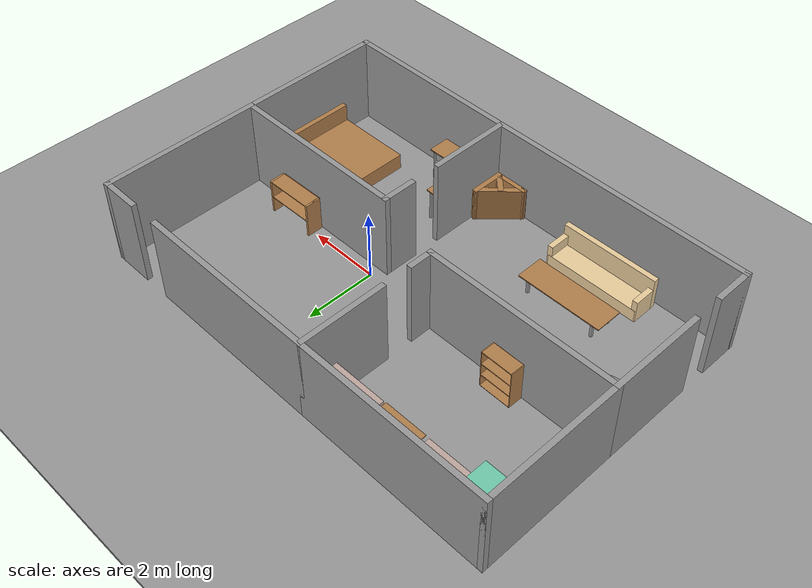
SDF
<sdf version="1.6">
 <world name="default">
  <light name="sun" type="directional">
   <pose>0 0 10 0 -0 0</pose>
   <diffuse>0.8 0.8 0.8 1</diffuse>
   <specular>0.2 0.2 0.2 1</specular>
   <attenuation>
    <range>1000</range>
    <constant>0.9</constant>
    <linear>0.01</linear>
    <quadratic>0.001</quadratic>
   </attenuation>
   <direction>-0.5 0.1 -0.9</direction>
  </light>
  <model name="ground_plane">
   <static>1</static>
   <link name="link">
    <collision name="collision">
     <geometry><plane><normal>0 0 1</normal><size>100 100</size></plane></geometry>
     <surface><friction><ode><mu>100</mu><mu2>50</mu2></ode></friction></surface>
    </collision>
    <visual name="visual">
     <cast_shadows>0</cast_shadows>
     <geometry><plane><normal>0 0 1</normal><size>100 100</size></plane></geometry>
     <material>
      <script><uri>file://media/materials/scripts/gazebo.material</uri><name>Gazebo/Grey</name></script>
     </material>
    </visual>
   </link>
  </model>
  <gravity>0 0 -9.8</gravity>
  <magnetic_field>6e-06 2.3e-05 -4.2e-05</magnetic_field>
  <atmosphere type="adiabatic"/>
  <physics name="default_physics" default="0" type="ode">
   <max_step_size>0.001</max_step_size>
   <real_time_factor>1</real_time_factor>
   <real_time_update_rate>1000</real_time_update_rate>
  </physics>
  <scene><ambient>0.4 0.4 0.4 1</ambient><background>0.7 0.7 0.7 1</background><shadows>1</shadows></scene>
  <spherical_coordinates>
   <surface_model>EARTH_WGS84</surface_model>
   <latitude_deg>0</latitude_deg>
   <longitude_deg>0</longitude_deg>
   <elevation>0</elevation>
   <heading_deg>0</heading_deg>
  </spherical_coordinates>
  <model name="wall">
   <pose>-1.40388 -0.16507 0 0 -0 0</pose>
   <link name="Wall_1">
    <collision name="Wall_1_Collision">
     <geometry><box><size>5.5 0.15 2.5</size></box></geometry>
     <pose>0 0 1.25 0 -0 0</pose>
    </collision>
    <visual name="Wall_1_Visual">
     <pose>0 0 1.25 0 -0 0</pose>
     <geometry><box><size>5.5 0.15 2.5</size></box></geometry>
     <material>
      <script><uri>file://media/materials/scripts/gazebo.material</uri><name>Gazebo/Grey</name></script>
      <ambient>1 1 1 1</ambient>
     </material>
     <meta><layer>0</layer></meta>
    </visual>
    <pose>-3.5 4.175 0 0 -0 0</pose>
   </link>
   <link name="Wall_11">
    <collision name="Wall_11_Collision">
     <geometry><box><size>2.75 0.15 2.5</size></box></geometry>
     <pose>0 0 1.25 0 -0 0</pose>
    </collision>
    <visual name="Wall_11_Visual">
     <pose>0 0 1.25 0 -0 0</pose>
     <geometry><box><size>2.75 0.15 2.5</size></box></geometry>
     <material>
      <script><uri>file://media/materials/scripts/gazebo.material</uri><name>Gazebo/Grey</name></script>
      <ambient>1 1 1 1</ambient>
     </material>
     <meta><layer>0</layer></meta>
    </visual>
    <pose>-6.175 -0.975 0 0 0 -1.5708</pose>
   </link>
   <link name="Wall_117">
    <collision name="Wall_117_Collision">
     <geometry><box><size>0.75 0.15 2.5</size></box></geometry>
     <pose>0 0 1.25 0 -0 0</pose>
    </collision>
    <visual name="Wall_117_Visual">
     <pose>0 0 1.25 0 -0 0</pose>
     <geometry><box><size>0.75 0.15 2.5</size></box></geometry>
     <material>
      <script><uri>file://media/materials/scripts/gazebo.material</uri><name>Gazebo/Grey</name></script>
      <ambient>1 1 1 1</ambient>
     </material>
     <meta><layer>0</layer></meta>
    </visual>
    <pose>-0.825 0.625 0 0 0 -1.5708</pose>
   </link>
   <link name="Wall_119">
    <collision name="Wall_119_Collision">
     <geometry><box><size>5.5 0.15 2.5</size></box></geometry>
     <pose>0 0 1.25 0 -0 0</pose>
    </collision>
    <visual name="Wall_119_Visual">
     <pose>0 0 1.25 0 -0 0</pose>
     <geometry><box><size>5.5 0.15 2.5</size></box></geometry>
     <material>
      <script><uri>file://media/materials/scripts/gazebo.material</uri><name>Gazebo/Grey</name></script>
      <ambient>1 1 1 1</ambient>
     </material>
     <meta><layer>0</layer></meta>
    </visual>
    <pose>-3.5 0.325 0 0 -0 3.14159</pose>
   </link>
   <link name="Wall_122">
    <collision name="Wall_122_Collision">
     <geometry><box><size>5.15 0.15 2.5</size></box></geometry>
     <pose>0 0 1.25 0 -0 0</pose>
    </collision>
    <visual name="Wall_122_Visual">
     <pose>0 0 1.25 0 -0 0</pose>
     <geometry><box><size>5.15 0.15 2.5</size></box></geometry>
     <material>
      <script><uri>file://media/materials/scripts/gazebo.material</uri><name>Gazebo/Grey</name></script>
      <ambient>1 1 1 1</ambient>
     </material>
     <meta><layer>0</layer></meta>
    </visual>
    <pose>3.675 -0.175 0 0 -0 3.14159</pose>
   </link>
   <link name="Wall_124">
    <collision name="Wall_124_Collision">
     <geometry><box><size>1 0.15 2.5</size></box></geometry>
     <pose>0 0 1.25 0 -0 0</pose>
    </collision>
    <visual name="Wall_124_Visual">
     <pose>0 0 1.25 0 -0 0</pose>
     <geometry><box><size>1 0.15 2.5</size></box></geometry>
     <material>
      <script><uri>file://media/materials/scripts/gazebo.material</uri><name>Gazebo/Grey</name></script>
      <ambient>1 1 1 1</ambient>
     </material>
     <meta><layer>0</layer></meta>
    </visual>
    <pose>1.175 -0.6 0 0 0 -1.5708</pose>
   </link>
   <link name="Wall_141">
    <collision name="Wall_141_Collision">
     <geometry><box><size>2.4 0.15 2.5</size></box></geometry>
     <pose>0 0 1.25 0 -0 0</pose>
    </collision>
    <visual name="Wall_141_Visual">
     <pose>0 0 1.25 0 -0 0</pose>
     <geometry><box><size>2.4 0.15 2.5</size></box></geometry>
     <material>
      <script><uri>file://media/materials/scripts/gazebo.material</uri><name>Gazebo/Grey</name></script>
      <ambient>1 1 1 1</ambient>
     </material>
     <meta><layer>0</layer></meta>
    </visual>
    <pose>1.175 -3.05 0 0 0 -1.5708</pose>
   </link>
   <link name="Wall_15">
    <collision name="Wall_15_Collision">
     <geometry><box><size>1.15 0.15 2.5</size></box></geometry>
     <pose>0 0 1.25 0 -0 0</pose>
    </collision>
    <visual name="Wall_15_Visual">
     <pose>0 0 1.25 0 -0 0</pose>
     <geometry><box><size>1.15 0.15 2.5</size></box></geometry>
     <material>
      <script><uri>file://media/materials/scripts/gazebo.material</uri><name>Gazebo/Grey</name></script>
      <ambient>1 1 1 1</ambient>
     </material>
     <meta><layer>0</layer></meta>
    </visual>
    <pose>-6.175 -3.675 0 0 0 -1.5708</pose>
   </link>
   <link name="Wall_17">
    <collision name="Wall_17_Collision">
     <geometry><box><size>7.5 0.15 2.5</size></box></geometry>
     <pose>0 0 1.25 0 -0 0</pose>
    </collision>
    <visual name="Wall_17_Visual">
     <pose>0 0 1.25 0 -0 0</pose>
     <geometry><box><size>7.5 0.15 2.5</size></box></geometry>
     <material>
      <script><uri>file://media/materials/scripts/gazebo.material</uri><name>Gazebo/Grey</name></script>
      <ambient>1 1 1 1</ambient>
     </material>
     <meta><layer>0</layer></meta>
    </visual>
    <pose>-2.5 -4.175 0 0 -0 0</pose>
   </link>
   <link name="Wall_18">
    <collision name="Wall_18_Collision">
     <geometry><box><size>5.15 0.15 2.5</size></box></geometry>
     <pose>0 0 1.25 0 -0 0</pose>
    </collision>
    <visual name="Wall_18_Visual">
     <pose>0 0 1.25 0 -0 0</pose>
     <geometry><box><size>5.15 0.15 2.5</size></box></geometry>
     <material>
      <script><uri>file://media/materials/scripts/gazebo.material</uri><name>Gazebo/Grey</name></script>
      <ambient>1 1 1 1</ambient>
     </material>
     <meta><layer>0</layer></meta>
    </visual>
    <pose>3.675 -4.175 0 0 -0 0</pose>
   </link>
   <link name="Wall_2">
    <collision name="Wall_2_Collision">
     <geometry><box><size>5.25 0.15 2.5</size></box></geometry>
     <pose>0 0 1.25 0 -0 0</pose>
    </collision>
    <visual name="Wall_2_Visual">
     <pose>0 0 1.25 0 -0 0</pose>
     <geometry><box><size>5.25 0.15 2.5</size></box></geometry>
     <material>
      <script><uri>file://media/materials/scripts/gazebo.material</uri><name>Gazebo/Grey</name></script>
      <ambient>1 1 1 1</ambient>
     </material>
     <meta><layer>0</layer></meta>
    </visual>
    <pose>1.725 4.175 0 0 -0 0</pose>
   </link>
   <link name="Wall_20">
    <collision name="Wall_20_Collision">
     <geometry><box><size>4.5 0.15 2.5</size></box></geometry>
     <pose>0 0 1.25 0 -0 0</pose>
    </collision>
    <visual name="Wall_20_Visual">
     <pose>0 0 1.25 0 -0 0</pose>
     <geometry><box><size>4.5 0.15 2.5</size></box></geometry>
     <material>
      <script><uri>file://media/materials/scripts/gazebo.material</uri><name>Gazebo/Grey</name></script>
      <ambient>1 1 1 1</ambient>
     </material>
     <meta><layer>0</layer></meta>
    </visual>
    <pose>6.175 2 0 0 0 -1.5708</pose>
   </link>
   <link name="Wall_21">
    <collision name="Wall_21_Collision">
     <geometry><box><size>4.15 0.15 2.5</size></box></geometry>
     <pose>0 0 1.25 0 -0 0</pose>
    </collision>
    <visual name="Wall_21_Visual">
     <pose>0 0 1.25 0 -0 0</pose>
     <geometry><box><size>4.15 0.15 2.5</size></box></geometry>
     <material>
      <script><uri>file://media/materials/scripts/gazebo.material</uri><name>Gazebo/Grey</name></script>
      <ambient>1 1 1 1</ambient>
     </material>
     <meta><layer>0</layer></meta>
    </visual>
    <pose>6.175 -2.175 0 0 0 -1.5708</pose>
   </link>
   <link name="Wall_26">
    <collision name="Wall_26_Collision">
     <geometry><box><size>2.5 0.15 2.5</size></box></geometry>
     <pose>0 0 1.25 0 -0 0</pose>
    </collision>
    <visual name="Wall_26_Visual">
     <pose>0 0 1.25 0 -0 0</pose>
     <geometry><box><size>2.5 0.15 2.5</size></box></geometry>
     <material>
      <script><uri>file://media/materials/scripts/gazebo.material</uri><name>Gazebo/Grey</name></script>
      <ambient>1 1 1 1</ambient>
     </material>
     <meta><layer>0</layer></meta>
    </visual>
    <pose>-0.825 3 0 0 0 -1.5708</pose>
   </link>
   <link name="Wall_5">
    <collision name="Wall_5_Collision">
     <geometry><box><size>1.15 0.15 2.5</size></box></geometry>
     <pose>0 0 1.25 0 -0 0</pose>
    </collision>
    <visual name="Wall_5_Visual">
     <pose>0 0 1.25 0 -0 0</pose>
     <geometry><box><size>1.15 0.15 2.5</size></box></geometry>
     <material>
      <script><uri>file://media/materials/scripts/gazebo.material</uri><name>Gazebo/Grey</name></script>
      <ambient>1 1 1 1</ambient>
     </material>
     <meta><layer>0</layer></meta>
    </visual>
    <pose>5.675 4.175 0 0 -0 0</pose>
   </link>
   <link name="Wall_7">
    <collision name="Wall_7_Collision">
     <geometry><box><size>4 0.15 2.5</size></box></geometry>
     <pose>0 0 1.25 0 -0 0</pose>
    </collision>
    <visual name="Wall_7_Visual">
     <pose>0 0 1.25 0 -0 0</pose>
     <geometry><box><size>4 0.15 2.5</size></box></geometry>
     <material>
      <script><uri>file://media/materials/scripts/gazebo.material</uri><name>Gazebo/Grey</name></script>
      <ambient>1 1 1 1</ambient>
     </material>
     <meta><layer>0</layer></meta>
    </visual>
    <pose>-6.175 2.25 0 0 0 -1.5708</pose>
   </link>
   <static>1</static>
  </model>
  <model name="bookshelf">
   <static>1</static>
   <link name="link">
    <inertial><mass>1</mass></inertial>
    <collision name="back">
     <pose>0 0.005 0.6 0 -0 0</pose>
     <geometry><box><size>0.9 0.01 1.2</size></box></geometry>
    </collision>
    <visual name="visual1">
     <pose>0 0.005 0.6 0 -0 0</pose>
     <geometry><box><size>0.9 0.01 1.2</size></box></geometry>
     <material>
      <script><uri>file://media/materials/scripts/gazebo.material</uri><name>Gazebo/Wood</name></script>
     </material>
    </visual>
    <collision name="left_side">
     <pose>0.45 -0.195 0.6 0 -0 0</pose>
     <geometry><box><size>0.02 0.4 1.2</size></box></geometry>
    </collision>
    <visual name="visual2">
     <pose>0.45 -0.195 0.6 0 -0 0</pose>
     <geometry><box><size>0.02 0.4 1.2</size></box></geometry>
     <material>
      <script><uri>file://media/materials/scripts/gazebo.material</uri><name>Gazebo/Wood</name></script>
     </material>
    </visual>
    <collision name="right_side">
     <pose>-0.45 -0.195 0.6 0 -0 0</pose>
     <geometry><box><size>0.02 0.4 1.2</size></box></geometry>
    </collision>
    <visual name="visual3">
     <pose>-0.45 -0.195 0.6 0 -0 0</pose>
     <geometry><box><size>0.02 0.4 1.2</size></box></geometry>
     <material>
      <script><uri>file://media/materials/scripts/gazebo.material</uri><name>Gazebo/Wood</name></script>
     </material>
    </visual>
    <collision name="bottom">
     <pose>0 -0.195 0.03 0 -0 0</pose>
     <geometry><box><size>0.88 0.4 0.06</size></box></geometry>
    </collision>
    <visual name="visual4">
     <pose>0 -0.195 0.03 0 -0 0</pose>
     <geometry><box><size>0.88 0.4 0.06</size></box></geometry>
     <material>
      <script><uri>file://media/materials/scripts/gazebo.material</uri><name>Gazebo/Wood</name></script>
     </material>
    </visual>
    <collision name="top">
     <pose>0 -0.195 1.19 0 -0 0</pose>
     <geometry><box><size>0.88 0.4 0.02</size></box></geometry>
    </collision>
    <visual name="visual5">
     <pose>0 -0.195 1.19 0 -0 0</pose>
     <geometry><box><size>0.88 0.4 0.02</size></box></geometry>
     <material>
      <script><uri>file://media/materials/scripts/gazebo.material</uri><name>Gazebo/Wood</name></script>
     </material>
    </visual>
    <collision name="low_shelf">
     <pose>0 -0.195 0.43 0 -0 0</pose>
     <geometry><box><size>0.88 0.4 0.02</size></box></geometry>
    </collision>
    <visual name="visual6">
     <pose>0 -0.195 0.43 0 -0 0</pose>
     <geometry><box><size>0.88 0.4 0.02</size></box></geometry>
     <material>
      <script><uri>file://media/materials/scripts/gazebo.material</uri><name>Gazebo/Wood</name></script>
     </material>
    </visual>
    <collision name="high_shelf">
     <pose>0 -0.195 0.8 0 -0 0</pose>
     <geometry><box><size>0.88 0.4 0.02</size></box></geometry>
    </collision>
    <visual name="visual7">
     <pose>0 -0.195 0.8 0 -0 0</pose>
     <geometry><box><size>0.88 0.4 0.02</size></box></geometry>
     <material>
      <script><uri>file://media/materials/scripts/gazebo.material</uri><name>Gazebo/Wood</name></script>
     </material>
    </visual>
   </link>
   <pose>2.71035 -0.426982 0 0 -0 0</pose>
  </model>
  <model name="cabinet_0">
   <link name="cabinet_bottom_plate">
    <pose>0.01959 0.54724 0.029947 0 -0 0</pose>
    <inertial>
     <pose>0 0 -0.0004 0 -0 0</pose>
     <inertia><ixx>11.2547</ixx><ixy>0</ixy><ixz>0</ixz><iyy>1.26163</iyy><iyz>0</iyz><izz>12.5113</izz></inertia>
     <mass>74.616</mass>
    </inertial>
    <visual name="cabinet_bottom_plate_geom_visual">
     <pose>0 0 0.01 0 -0 0</pose>
     <geometry><box><size>0.45 1.34522 0.02</size></box></geometry>
     <material>
      <script><uri>file://media/materials/scripts/gazebo.material</uri><name>Gazebo/Wood</name></script>
      <shader type="pixel"><normal_map>__default__</normal_map></shader>
      <ambient>1 1 1 1</ambient>
      <diffuse>1 1 1 1</diffuse>
      <specular>0.2 0.2 0.2 1</specular>
      <emissive>0 0 0 1</emissive>
     </material>
    </visual>
    <visual name="cabinet_bottom_plate_geom_cabinet_back_plate_visual">
     <pose>0.235 0 0.51 0 -0 0</pose>
     <geometry><box><size>0.02 1.34522 1.02</size></box></geometry>
     <material>
      <script><uri>file://media/materials/scripts/gazebo.material</uri><name>Gazebo/Wood</name></script>
      <shader type="pixel"><normal_map>__default__</normal_map></shader>
      <ambient>1 1 1 1</ambient>
      <diffuse>1 1 1 1</diffuse>
      <specular>0.2 0.2 0.2 1</specular>
      <emissive>0 0 0 1</emissive>
     </material>
    </visual>
    <visual name="cabinet_bottom_plate_geom_cabinet_left_plate_visual">
     <pose>0 0.672609 0.51 0 -0 0</pose>
     <geometry><box><size>0.45 0.059588 1.02</size></box></geometry>
     <material>
      <script><uri>file://media/materials/scripts/gazebo.material</uri><name>Gazebo/Wood</name></script>
      <shader type="pixel"><normal_map>__default__</normal_map></shader>
      <ambient>1 1 1 1</ambient>
      <diffuse>1 1 1 1</diffuse>
      <specular>0.2 0.2 0.2 1</specular>
      <emissive>0 0 0 1</emissive>
     </material>
    </visual>
    <visual name="cabinet_bottom_plate_geom_cabinet_middle_plate_visual">
     <pose>0 0 0.51 0 -0 0</pose>
     <geometry><box><size>0.45 1.34522 0.02</size></box></geometry>
     <material>
      <script><uri>file://media/materials/scripts/gazebo.material</uri><name>Gazebo/Wood</name></script>
      <shader type="pixel"><normal_map>__default__</normal_map></shader>
      <ambient>1 1 1 1</ambient>
      <diffuse>1 1 1 1</diffuse>
      <specular>0.2 0.2 0.2 1</specular>
      <emissive>0 0 0 1</emissive>
     </material>
    </visual>
    <visual name="cabinet_bottom_plate_geom_cabinet_right_plate_visual">
     <pose>0 -0.672609 0.51 0 -0 0</pose>
     <geometry><box><size>0.45 0.059588 1.02</size></box></geometry>
     <material>
      <script><uri>file://media/materials/scripts/gazebo.material</uri><name>Gazebo/Wood</name></script>
      <shader type="pixel"><normal_map>__default__</normal_map></shader>
      <ambient>1 1 1 1</ambient>
      <diffuse>1 1 1 1</diffuse>
      <specular>0.2 0.2 0.2 1</specular>
      <emissive>0 0 0 1</emissive>
     </material>
    </visual>
    <visual name="cabinet_bottom_plate_geom_cabinet_top_plate_visual">
     <pose>0 0 1.01 0 -0 0</pose>
     <geometry><box><size>0.45 1.34522 0.02</size></box></geometry>
     <material>
      <script><uri>file://media/materials/scripts/gazebo.material</uri><name>Gazebo/Wood</name></script>
      <shader type="pixel"><normal_map>__default__</normal_map></shader>
      <ambient>1 1 1 1</ambient>
      <diffuse>1 1 1 1</diffuse>
      <specular>0.2 0.2 0.2 1</specular>
      <emissive>0 0 0 1</emissive>
     </material>
    </visual>
    <collision name="cabinet_bottom_plate_geom">
     <pose>0 0 0.01 0 -0 0</pose>
     <geometry><box><size>0.45 1.34522 0.02</size></box></geometry>
     <surface>
      <friction>
       <ode><mu>1</mu><mu2>1</mu2><fdir1>0 0 0</fdir1><slip1>0</slip1><slip2>0</slip2></ode>
       <torsional>
        <coefficient>1</coefficient>
        <patch_radius>0</patch_radius>
        <surface_radius>0</surface_radius>
        <use_patch_radius>1</use_patch_radius>
        <ode><slip>0</slip></ode>
       </torsional>
      </friction>
      <bounce><restitution_coefficient>0</restitution_coefficient><threshold>1e+06</threshold></bounce>
      <contact>
       <collide_without_contact>0</collide_without_contact>
       <collide_without_contact_bitmask>1</collide_without_contact_bitmask>
       <collide_bitmask>1</collide_bitmask>
       <ode>
        <soft_cfm>0</soft_cfm>
        <soft_erp>0.2</soft_erp>
        <kp>1e+13</kp>
        <kd>1</kd>
        <max_vel>0.01</max_vel>
        <min_depth>0</min_depth>
       </ode>
       <bullet>
        <split_impulse>1</split_impulse>
        <split_impulse_penetration_threshold>-0.01</split_impulse_penetration_threshold>
        <soft_cfm>0</soft_cfm>
        <soft_erp>0.2</soft_erp>
        <kp>1e+13</kp>
        <kd>1</kd>
       </bullet>
      </contact>
     </surface>
    </collision>
    <collision name="cabinet_bottom_plate_geom_cabinet_back_plate">
     <pose>0.235 0 0.51 0 -0 0</pose>
     <geometry><box><size>0.02 1.34523 1.02</size></box></geometry>
     <surface>
      <friction>
       <ode><mu>1</mu><mu2>1</mu2><fdir1>0 0 0</fdir1><slip1>0</slip1><slip2>0</slip2></ode>
       <torsional>
        <coefficient>1</coefficient>
        <patch_radius>0</patch_radius>
        <surface_radius>0</surface_radius>
        <use_patch_radius>1</use_patch_radius>
        <ode><slip>0</slip></ode>
       </torsional>
      </friction>
      <bounce><restitution_coefficient>0</restitution_coefficient><threshold>1e+06</threshold></bounce>
      <contact>
       <collide_without_contact>0</collide_without_contact>
       <collide_without_contact_bitmask>1</collide_without_contact_bitmask>
       <collide_bitmask>1</collide_bitmask>
       <ode>
        <soft_cfm>0</soft_cfm>
        <soft_erp>0.2</soft_erp>
        <kp>1e+13</kp>
        <kd>1</kd>
        <max_vel>0.01</max_vel>
        <min_depth>0</min_depth>
       </ode>
       <bullet>
        <split_impulse>1</split_impulse>
        <split_impulse_penetration_threshold>-0.01</split_impulse_penetration_threshold>
        <soft_cfm>0</soft_cfm>
        <soft_erp>0.2</soft_erp>
        <kp>1e+13</kp>
        <kd>1</kd>
       </bullet>
      </contact>
     </surface>
    </collision>
    <collision name="cabinet_bottom_plate_geom_cabinet_middle_plate">
     <pose>0 0 0.51 0 -0 0</pose>
     <geometry><box><size>0.45 1.34522 0.02</size></box></geometry>
     <surface>
      <friction>
       <ode><mu>1</mu><mu2>1</mu2><fdir1>0 0 0</fdir1><slip1>0</slip1><slip2>0</slip2></ode>
       <torsional>
        <coefficient>1</coefficient>
        <patch_radius>0</patch_radius>
        <surface_radius>0</surface_radius>
        <use_patch_radius>1</use_patch_radius>
        <ode><slip>0</slip></ode>
       </torsional>
      </friction>
      <bounce><restitution_coefficient>0</restitution_coefficient><threshold>1e+06</threshold></bounce>
      <contact>
       <collide_without_contact>0</collide_without_contact>
       <collide_without_contact_bitmask>1</collide_without_contact_bitmask>
       <collide_bitmask>1</collide_bitmask>
       <ode>
        <soft_cfm>0</soft_cfm>
        <soft_erp>0.2</soft_erp>
        <kp>1e+13</kp>
        <kd>1</kd>
        <max_vel>0.01</max_vel>
        <min_depth>0</min_depth>
       </ode>
       <bullet>
        <split_impulse>1</split_impulse>
        <split_impulse_penetration_threshold>-0.01</split_impulse_penetration_threshold>
        <soft_cfm>0</soft_cfm>
        <soft_erp>0.2</soft_erp>
        <kp>1e+13</kp>
        <kd>1</kd>
       </bullet>
      </contact>
     </surface>
    </collision>
    <collision name="cabinet_bottom_plate_geom_cabinet_left_plate">
     <pose>0 0.672609 0.51 0 -0 0</pose>
     <geometry><box><size>0.45 0.059588 1.02</size></box></geometry>
     <surface>
      <friction>
       <ode><mu>1</mu><mu2>1</mu2><fdir1>0 0 0</fdir1><slip1>0</slip1><slip2>0</slip2></ode>
       <torsional>
        <coefficient>1</coefficient>
        <patch_radius>0</patch_radius>
        <surface_radius>0</surface_radius>
        <use_patch_radius>1</use_patch_radius>
        <ode><slip>0</slip></ode>
       </torsional>
      </friction>
      <bounce><restitution_coefficient>0</restitution_coefficient><threshold>1e+06</threshold></bounce>
      <contact>
       <collide_without_contact>0</collide_without_contact>
       <collide_without_contact_bitmask>1</collide_without_contact_bitmask>
       <collide_bitmask>1</collide_bitmask>
       <ode>
        <soft_cfm>0</soft_cfm>
        <soft_erp>0.2</soft_erp>
        <kp>1e+13</kp>
        <kd>1</kd>
        <max_vel>0.01</max_vel>
        <min_depth>0</min_depth>
       </ode>
       <bullet>
        <split_impulse>1</split_impulse>
        <split_impulse_penetration_threshold>-0.01</split_impulse_penetration_threshold>
        <soft_cfm>0</soft_cfm>
        <soft_erp>0.2</soft_erp>
        <kp>1e+13</kp>
        <kd>1</kd>
       </bullet>
      </contact>
     </surface>
    </collision>
    <collision name="cabinet_bottom_plate_geom_cabinet_right_plate">
     <pose>0 -0.672609 0.51 0 -0 0</pose>
     <geometry><box><size>0.45 0.059588 1.02</size></box></geometry>
     <surface>
      <friction>
       <ode><mu>1</mu><mu2>1</mu2><fdir1>0 0 0</fdir1><slip1>0</slip1><slip2>0</slip2></ode>
       <torsional>
        <coefficient>1</coefficient>
        <patch_radius>0</patch_radius>
        <surface_radius>0</surface_radius>
        <use_patch_radius>1</use_patch_radius>
        <ode><slip>0</slip></ode>
       </torsional>
      </friction>
      <bounce><restitution_coefficient>0</restitution_coefficient><threshold>1e+06</threshold></bounce>
      <contact>
       <collide_without_contact>0</collide_without_contact>
       <collide_without_contact_bitmask>1</collide_without_contact_bitmask>
       <collide_bitmask>1</collide_bitmask>
       <ode>
        <soft_cfm>0</soft_cfm>
        <soft_erp>0.2</soft_erp>
        <kp>1e+13</kp>
        <kd>1</kd>
        <max_vel>0.01</max_vel>
        <min_depth>0</min_depth>
       </ode>
       <bullet>
        <split_impulse>1</split_impulse>
        <split_impulse_penetration_threshold>-0.01</split_impulse_penetration_threshold>
        <soft_cfm>0</soft_cfm>
        <soft_erp>0.2</soft_erp>
        <kp>1e+13</kp>
        <kd>1</kd>
       </bullet>
      </contact>
     </surface>
    </collision>
    <collision name="cabinet_bottom_plate_geom_cabinet_top_plate">
     <pose>0 0 1.01 0 -0 0</pose>
     <geometry><box><size>0.45 1.34522 0.02</size></box></geometry>
     <surface>
      <friction>
       <ode><mu>1</mu><mu2>1</mu2><fdir1>0 0 0</fdir1><slip1>0</slip1><slip2>0</slip2></ode>
       <torsional>
        <coefficient>1</coefficient>
        <patch_radius>0</patch_radius>
        <surface_radius>0</surface_radius>
        <use_patch_radius>1</use_patch_radius>
        <ode><slip>0</slip></ode>
       </torsional>
      </friction>
      <bounce><restitution_coefficient>0</restitution_coefficient><threshold>1e+06</threshold></bounce>
      <contact>
       <collide_without_contact>0</collide_without_contact>
       <collide_without_contact_bitmask>1</collide_without_contact_bitmask>
       <collide_bitmask>1</collide_bitmask>
       <ode>
        <soft_cfm>0</soft_cfm>
        <soft_erp>0.2</soft_erp>
        <kp>1e+13</kp>
        <kd>1</kd>
        <max_vel>0.01</max_vel>
        <min_depth>0</min_depth>
       </ode>
       <bullet>
        <split_impulse>1</split_impulse>
        <split_impulse_penetration_threshold>-0.01</split_impulse_penetration_threshold>
        <soft_cfm>0</soft_cfm>
        <soft_erp>0.2</soft_erp>
        <kp>1e+13</kp>
        <kd>1</kd>
       </bullet>
      </contact>
     </surface>
    </collision>
   </link>
   <static>1</static>
   <pose>2.26774 0.007381 0 0 0 -1.55636</pose>
  </model>
  <model name="table_0">
   <link name="link">
    <pose>0.121367 0.101535 0 0 -0 0</pose>
    <inertial>
     <inertia><ixx>0</ixx><ixy>0</ixy><ixz>0</ixz><iyy>0</iyy><iyz>0</iyz><izz>0</izz></inertia>
     <mass>0</mass>
    </inertial>
    <visual name="visual1">
     <pose>0 0 1 0 -0 0</pose>
     <geometry><box><size>1.0961 0.633078 0.03</size></box></geometry>
     <material>
      <script><uri>file://media/materials/scripts/gazebo.material</uri><name>Gazebo/Wood</name></script>
      <shader type="pixel"><normal_map>__default__</normal_map></shader>
      <ambient>1 1 1 1</ambient>
      <diffuse>1 1 1 1</diffuse>
      <specular>0.2 0.2 0.2 1</specular>
      <emissive>0 0 0 1</emissive>
     </material>
    </visual>
    <visual name="front_right_leg">
     <pose>0.45 -0.25 0.5 0 -0 0</pose>
     <geometry><cylinder><radius>0.0304</radius><length>1</length></cylinder></geometry>
     <material>
      <script><uri>file://media/materials/scripts/gazebo.material</uri><name>Gazebo/Grey</name></script>
      <shader type="pixel"><normal_map>__default__</normal_map></shader>
      <ambient>0.3 0.3 0.3 1</ambient>
      <diffuse>0.7 0.7 0.7 1</diffuse>
      <specular>0.01 0.01 0.01 1</specular>
      <emissive>0 0 0 1</emissive>
     </material>
    </visual>
    <visual name="front_left_leg">
     <pose>0.45 0.25 0.5 0 -0 0</pose>
     <geometry><cylinder><radius>0.0304</radius><length>1</length></cylinder></geometry>
     <material>
      <script><uri>file://media/materials/scripts/gazebo.material</uri><name>Gazebo/Grey</name></script>
      <shader type="pixel"><normal_map>__default__</normal_map></shader>
      <ambient>0.3 0.3 0.3 1</ambient>
      <diffuse>0.7 0.7 0.7 1</diffuse>
      <specular>0.01 0.01 0.01 1</specular>
      <emissive>0 0 0 1</emissive>
     </material>
    </visual>
    <visual name="back_right_leg">
     <pose>-0.45 -0.25 0.5 0 -0 0</pose>
     <geometry><cylinder><radius>0.0304</radius><length>1</length></cylinder></geometry>
     <material>
      <script><uri>file://media/materials/scripts/gazebo.material</uri><name>Gazebo/Grey</name></script>
      <shader type="pixel"><normal_map>__default__</normal_map></shader>
      <ambient>0.3 0.3 0.3 1</ambient>
      <diffuse>0.7 0.7 0.7 1</diffuse>
      <specular>0.01 0.01 0.01 1</specular>
      <emissive>0 0 0 1</emissive>
     </material>
    </visual>
    <visual name="back_left_leg">
     <pose>-0.45 0.25 0.5 0 -0 0</pose>
     <geometry><cylinder><radius>0.0304</radius><length>1</length></cylinder></geometry>
     <material>
      <script><uri>file://media/materials/scripts/gazebo.material</uri><name>Gazebo/Grey</name></script>
      <shader type="pixel"><normal_map>__default__</normal_map></shader>
      <ambient>0.3 0.3 0.3 1</ambient>
      <diffuse>0.7 0.7 0.7 1</diffuse>
      <specular>0.01 0.01 0.01 1</specular>
      <emissive>0 0 0 1</emissive>
     </material>
    </visual>
    <collision name="surface">
     <pose>0 0 1 0 -0 0</pose>
     <geometry><box><size>1.0961 0.633078 0.03</size></box></geometry>
     <surface>
      <friction>
       <ode><mu>0.6</mu><mu2>0.6</mu2><fdir1>0 0 0</fdir1><slip1>0</slip1><slip2>0</slip2></ode>
       <torsional>
        <coefficient>1</coefficient>
        <patch_radius>0</patch_radius>
        <surface_radius>0</surface_radius>
        <use_patch_radius>1</use_patch_radius>
        <ode><slip>0</slip></ode>
       </torsional>
      </friction>
      <bounce><restitution_coefficient>0</restitution_coefficient><threshold>1e+06</threshold></bounce>
      <contact>
       <collide_without_contact>0</collide_without_contact>
       <collide_without_contact_bitmask>1</collide_without_contact_bitmask>
       <collide_bitmask>1</collide_bitmask>
       <ode>
        <soft_cfm>0</soft_cfm>
        <soft_erp>0.2</soft_erp>
        <kp>1e+13</kp>
        <kd>1</kd>
        <max_vel>0.01</max_vel>
        <min_depth>0</min_depth>
       </ode>
       <bullet>
        <split_impulse>1</split_impulse>
        <split_impulse_penetration_threshold>-0.01</split_impulse_penetration_threshold>
        <soft_cfm>0</soft_cfm>
        <soft_erp>0.2</soft_erp>
        <kp>1e+13</kp>
        <kd>1</kd>
       </bullet>
      </contact>
     </surface>
    </collision>
    <collision name="front_left_leg">
     <pose>0.45 0.25 0.5 0 -0 0</pose>
     <geometry><cylinder><radius>0.0304</radius><length>1</length></cylinder></geometry>
     <surface>
      <friction>
       <ode><mu>1</mu><mu2>1</mu2><fdir1>0 0 0</fdir1><slip1>0</slip1><slip2>0</slip2></ode>
       <torsional>
        <coefficient>1</coefficient>
        <patch_radius>0</patch_radius>
        <surface_radius>0</surface_radius>
        <use_patch_radius>1</use_patch_radius>
        <ode><slip>0</slip></ode>
       </torsional>
      </friction>
      <bounce><restitution_coefficient>0</restitution_coefficient><threshold>1e+06</threshold></bounce>
      <contact>
       <collide_without_contact>0</collide_without_contact>
       <collide_without_contact_bitmask>1</collide_without_contact_bitmask>
       <collide_bitmask>1</collide_bitmask>
       <ode>
        <soft_cfm>0</soft_cfm>
        <soft_erp>0.2</soft_erp>
        <kp>1e+13</kp>
        <kd>1</kd>
        <max_vel>0.01</max_vel>
        <min_depth>0</min_depth>
       </ode>
       <bullet>
        <split_impulse>1</split_impulse>
        <split_impulse_penetration_threshold>-0.01</split_impulse_penetration_threshold>
        <soft_cfm>0</soft_cfm>
        <soft_erp>0.2</soft_erp>
        <kp>1e+13</kp>
        <kd>1</kd>
       </bullet>
      </contact>
     </surface>
    </collision>
    <collision name="front_right_leg">
     <pose>0.45 -0.25 0.5 0 -0 0</pose>
     <geometry><cylinder><radius>0.0304</radius><length>1</length></cylinder></geometry>
     <surface>
      <friction>
       <ode><mu>1</mu><mu2>1</mu2><fdir1>0 0 0</fdir1><slip1>0</slip1><slip2>0</slip2></ode>
       <torsional>
        <coefficient>1</coefficient>
        <patch_radius>0</patch_radius>
        <surface_radius>0</surface_radius>
        <use_patch_radius>1</use_patch_radius>
        <ode><slip>0</slip></ode>
       </torsional>
      </friction>
      <bounce><restitution_coefficient>0</restitution_coefficient><threshold>1e+06</threshold></bounce>
      <contact>
       <collide_without_contact>0</collide_without_contact>
       <collide_without_contact_bitmask>1</collide_without_contact_bitmask>
       <collide_bitmask>1</collide_bitmask>
       <ode>
        <soft_cfm>0</soft_cfm>
        <soft_erp>0.2</soft_erp>
        <kp>1e+13</kp>
        <kd>1</kd>
        <max_vel>0.01</max_vel>
        <min_depth>0</min_depth>
       </ode>
       <bullet>
        <split_impulse>1</split_impulse>
        <split_impulse_penetration_threshold>-0.01</split_impulse_penetration_threshold>
        <soft_cfm>0</soft_cfm>
        <soft_erp>0.2</soft_erp>
        <kp>1e+13</kp>
        <kd>1</kd>
       </bullet>
      </contact>
     </surface>
    </collision>
    <collision name="back_right_leg">
     <pose>-0.45 -0.25 0.5 0 -0 0</pose>
     <geometry><cylinder><radius>0.0304</radius><length>1</length></cylinder></geometry>
     <surface>
      <friction>
       <ode><mu>1</mu><mu2>1</mu2><fdir1>0 0 0</fdir1><slip1>0</slip1><slip2>0</slip2></ode>
       <torsional>
        <coefficient>1</coefficient>
        <patch_radius>0</patch_radius>
        <surface_radius>0</surface_radius>
        <use_patch_radius>1</use_patch_radius>
        <ode><slip>0</slip></ode>
       </torsional>
      </friction>
      <bounce><restitution_coefficient>0</restitution_coefficient><threshold>1e+06</threshold></bounce>
      <contact>
       <collide_without_contact>0</collide_without_contact>
       <collide_without_contact_bitmask>1</collide_without_contact_bitmask>
       <collide_bitmask>1</collide_bitmask>
       <ode>
        <soft_cfm>0</soft_cfm>
        <soft_erp>0.2</soft_erp>
        <kp>1e+13</kp>
        <kd>1</kd>
        <max_vel>0.01</max_vel>
        <min_depth>0</min_depth>
       </ode>
       <bullet>
        <split_impulse>1</split_impulse>
        <split_impulse_penetration_threshold>-0.01</split_impulse_penetration_threshold>
        <soft_cfm>0</soft_cfm>
        <soft_erp>0.2</soft_erp>
        <kp>1e+13</kp>
        <kd>1</kd>
       </bullet>
      </contact>
     </surface>
    </collision>
    <collision name="back_left_leg">
     <pose>-0.45 0.25 0.5 0 -0 0</pose>
     <geometry><cylinder><radius>0.0304</radius><length>1</length></cylinder></geometry>
     <surface>
      <friction>
       <ode><mu>1</mu><mu2>1</mu2><fdir1>0 0 0</fdir1><slip1>0</slip1><slip2>0</slip2></ode>
       <torsional>
        <coefficient>1</coefficient>
        <patch_radius>0</patch_radius>
        <surface_radius>0</surface_radius>
        <use_patch_radius>1</use_patch_radius>
        <ode><slip>0</slip></ode>
       </torsional>
      </friction>
      <bounce><restitution_coefficient>0</restitution_coefficient><threshold>1e+06</threshold></bounce>
      <contact>
       <collide_without_contact>0</collide_without_contact>
       <collide_without_contact_bitmask>1</collide_without_contact_bitmask>
       <collide_bitmask>1</collide_bitmask>
       <ode>
        <soft_cfm>0</soft_cfm>
        <soft_erp>0.2</soft_erp>
        <kp>1e+13</kp>
        <kd>1</kd>
        <max_vel>0.01</max_vel>
        <min_depth>0</min_depth>
       </ode>
       <bullet>
        <split_impulse>1</split_impulse>
        <split_impulse_penetration_threshold>-0.01</split_impulse_penetration_threshold>
        <soft_cfm>0</soft_cfm>
        <soft_erp>0.2</soft_erp>
        <kp>1e+13</kp>
        <kd>1</kd>
       </bullet>
      </contact>
     </surface>
    </collision>
   </link>
   <static>1</static>
   <pose>-1.71409 3.51433 0 0 -0 0</pose>
  </model>
  <model name="table_0_0">
   <link name="link">
    <pose>0.121367 0.101535 0 0 -0 0</pose>
    <inertial>
     <inertia><ixx>0</ixx><ixy>0</ixy><ixz>0</ixz><iyy>0</iyy><iyz>0</iyz><izz>0</izz></inertia>
     <mass>0</mass>
    </inertial>
    <visual name="visual1">
     <pose>0 0 1 0 -0 0</pose>
     <geometry><box><size>1.0961 0.633078 0.03</size></box></geometry>
     <material>
      <script><uri>file://media/materials/scripts/gazebo.material</uri><name>Gazebo/Wood</name></script>
      <shader type="pixel"><normal_map>__default__</normal_map></shader>
      <ambient>1 1 1 1</ambient>
      <diffuse>1 1 1 1</diffuse>
      <specular>0.2 0.2 0.2 1</specular>
      <emissive>0 0 0 1</emissive>
     </material>
    </visual>
    <visual name="front_right_leg">
     <pose>0.45 -0.25 0.5 0 -0 0</pose>
     <geometry><cylinder><radius>0.0304</radius><length>1</length></cylinder></geometry>
     <material>
      <script><uri>file://media/materials/scripts/gazebo.material</uri><name>Gazebo/Grey</name></script>
      <shader type="pixel"><normal_map>__default__</normal_map></shader>
      <ambient>0.3 0.3 0.3 1</ambient>
      <diffuse>0.7 0.7 0.7 1</diffuse>
      <specular>0.01 0.01 0.01 1</specular>
      <emissive>0 0 0 1</emissive>
     </material>
    </visual>
    <visual name="front_left_leg">
     <pose>0.45 0.25 0.5 0 -0 0</pose>
     <geometry><cylinder><radius>0.0304</radius><length>1</length></cylinder></geometry>
     <material>
      <script><uri>file://media/materials/scripts/gazebo.material</uri><name>Gazebo/Grey</name></script>
      <shader type="pixel"><normal_map>__default__</normal_map></shader>
      <ambient>0.3 0.3 0.3 1</ambient>
      <diffuse>0.7 0.7 0.7 1</diffuse>
      <specular>0.01 0.01 0.01 1</specular>
      <emissive>0 0 0 1</emissive>
     </material>
    </visual>
    <visual name="back_right_leg">
     <pose>-0.45 -0.25 0.5 0 -0 0</pose>
     <geometry><cylinder><radius>0.0304</radius><length>1</length></cylinder></geometry>
     <material>
      <script><uri>file://media/materials/scripts/gazebo.material</uri><name>Gazebo/Grey</name></script>
      <shader type="pixel"><normal_map>__default__</normal_map></shader>
      <ambient>0.3 0.3 0.3 1</ambient>
      <diffuse>0.7 0.7 0.7 1</diffuse>
      <specular>0.01 0.01 0.01 1</specular>
      <emissive>0 0 0 1</emissive>
     </material>
    </visual>
    <visual name="back_left_leg">
     <pose>-0.45 0.25 0.5 0 -0 0</pose>
     <geometry><cylinder><radius>0.0304</radius><length>1</length></cylinder></geometry>
     <material>
      <script><uri>file://media/materials/scripts/gazebo.material</uri><name>Gazebo/Grey</name></script>
      <shader type="pixel"><normal_map>__default__</normal_map></shader>
      <ambient>0.3 0.3 0.3 1</ambient>
      <diffuse>0.7 0.7 0.7 1</diffuse>
      <specular>0.01 0.01 0.01 1</specular>
      <emissive>0 0 0 1</emissive>
     </material>
    </visual>
    <collision name="surface">
     <pose>0 0 1 0 -0 0</pose>
     <geometry><box><size>1.0961 0.633078 0.03</size></box></geometry>
     <surface>
      <friction>
       <ode><mu>0.6</mu><mu2>0.6</mu2><fdir1>0 0 0</fdir1><slip1>0</slip1><slip2>0</slip2></ode>
       <torsional>
        <coefficient>1</coefficient>
        <patch_radius>0</patch_radius>
        <surface_radius>0</surface_radius>
        <use_patch_radius>1</use_patch_radius>
        <ode><slip>0</slip></ode>
       </torsional>
      </friction>
      <bounce><restitution_coefficient>0</restitution_coefficient><threshold>1e+06</threshold></bounce>
      <contact>
       <collide_without_contact>0</collide_without_contact>
       <collide_without_contact_bitmask>1</collide_without_contact_bitmask>
       <collide_bitmask>1</collide_bitmask>
       <ode>
        <soft_cfm>0</soft_cfm>
        <soft_erp>0.2</soft_erp>
        <kp>1e+13</kp>
        <kd>1</kd>
        <max_vel>0.01</max_vel>
        <min_depth>0</min_depth>
       </ode>
       <bullet>
        <split_impulse>1</split_impulse>
        <split_impulse_penetration_threshold>-0.01</split_impulse_penetration_threshold>
        <soft_cfm>0</soft_cfm>
        <soft_erp>0.2</soft_erp>
        <kp>1e+13</kp>
        <kd>1</kd>
       </bullet>
      </contact>
     </surface>
    </collision>
    <collision name="front_left_leg">
     <pose>0.45 0.25 0.5 0 -0 0</pose>
     <geometry><cylinder><radius>0.0304</radius><length>1</length></cylinder></geometry>
     <surface>
      <friction>
       <ode><mu>1</mu><mu2>1</mu2><fdir1>0 0 0</fdir1><slip1>0</slip1><slip2>0</slip2></ode>
       <torsional>
        <coefficient>1</coefficient>
        <patch_radius>0</patch_radius>
        <surface_radius>0</surface_radius>
        <use_patch_radius>1</use_patch_radius>
        <ode><slip>0</slip></ode>
       </torsional>
      </friction>
      <bounce><restitution_coefficient>0</restitution_coefficient><threshold>1e+06</threshold></bounce>
      <contact>
       <collide_without_contact>0</collide_without_contact>
       <collide_without_contact_bitmask>1</collide_without_contact_bitmask>
       <collide_bitmask>1</collide_bitmask>
       <ode>
        <soft_cfm>0</soft_cfm>
        <soft_erp>0.2</soft_erp>
        <kp>1e+13</kp>
        <kd>1</kd>
        <max_vel>0.01</max_vel>
        <min_depth>0</min_depth>
       </ode>
       <bullet>
        <split_impulse>1</split_impulse>
        <split_impulse_penetration_threshold>-0.01</split_impulse_penetration_threshold>
        <soft_cfm>0</soft_cfm>
        <soft_erp>0.2</soft_erp>
        <kp>1e+13</kp>
        <kd>1</kd>
       </bullet>
      </contact>
     </surface>
    </collision>
    <collision name="front_right_leg">
     <pose>0.45 -0.25 0.5 0 -0 0</pose>
     <geometry><cylinder><radius>0.0304</radius><length>1</length></cylinder></geometry>
     <surface>
      <friction>
       <ode><mu>1</mu><mu2>1</mu2><fdir1>0 0 0</fdir1><slip1>0</slip1><slip2>0</slip2></ode>
       <torsional>
        <coefficient>1</coefficient>
        <patch_radius>0</patch_radius>
        <surface_radius>0</surface_radius>
        <use_patch_radius>1</use_patch_radius>
        <ode><slip>0</slip></ode>
       </torsional>
      </friction>
      <bounce><restitution_coefficient>0</restitution_coefficient><threshold>1e+06</threshold></bounce>
      <contact>
       <collide_without_contact>0</collide_without_contact>
       <collide_without_contact_bitmask>1</collide_without_contact_bitmask>
       <collide_bitmask>1</collide_bitmask>
       <ode>
        <soft_cfm>0</soft_cfm>
        <soft_erp>0.2</soft_erp>
        <kp>1e+13</kp>
        <kd>1</kd>
        <max_vel>0.01</max_vel>
        <min_depth>0</min_depth>
       </ode>
       <bullet>
        <split_impulse>1</split_impulse>
        <split_impulse_penetration_threshold>-0.01</split_impulse_penetration_threshold>
        <soft_cfm>0</soft_cfm>
        <soft_erp>0.2</soft_erp>
        <kp>1e+13</kp>
        <kd>1</kd>
       </bullet>
      </contact>
     </surface>
    </collision>
    <collision name="back_right_leg">
     <pose>-0.45 -0.25 0.5 0 -0 0</pose>
     <geometry><cylinder><radius>0.0304</radius><length>1</length></cylinder></geometry>
     <surface>
      <friction>
       <ode><mu>1</mu><mu2>1</mu2><fdir1>0 0 0</fdir1><slip1>0</slip1><slip2>0</slip2></ode>
       <torsional>
        <coefficient>1</coefficient>
        <patch_radius>0</patch_radius>
        <surface_radius>0</surface_radius>
        <use_patch_radius>1</use_patch_radius>
        <ode><slip>0</slip></ode>
       </torsional>
      </friction>
      <bounce><restitution_coefficient>0</restitution_coefficient><threshold>1e+06</threshold></bounce>
      <contact>
       <collide_without_contact>0</collide_without_contact>
       <collide_without_contact_bitmask>1</collide_without_contact_bitmask>
       <collide_bitmask>1</collide_bitmask>
       <ode>
        <soft_cfm>0</soft_cfm>
        <soft_erp>0.2</soft_erp>
        <kp>1e+13</kp>
        <kd>1</kd>
        <max_vel>0.01</max_vel>
        <min_depth>0</min_depth>
       </ode>
       <bullet>
        <split_impulse>1</split_impulse>
        <split_impulse_penetration_threshold>-0.01</split_impulse_penetration_threshold>
        <soft_cfm>0</soft_cfm>
        <soft_erp>0.2</soft_erp>
        <kp>1e+13</kp>
        <kd>1</kd>
       </bullet>
      </contact>
     </surface>
    </collision>
    <collision name="back_left_leg">
     <pose>-0.45 0.25 0.5 0 -0 0</pose>
     <geometry><cylinder><radius>0.0304</radius><length>1</length></cylinder></geometry>
     <surface>
      <friction>
       <ode><mu>1</mu><mu2>1</mu2><fdir1>0 0 0</fdir1><slip1>0</slip1><slip2>0</slip2></ode>
       <torsional>
        <coefficient>1</coefficient>
        <patch_radius>0</patch_radius>
        <surface_radius>0</surface_radius>
        <use_patch_radius>1</use_patch_radius>
        <ode><slip>0</slip></ode>
       </torsional>
      </friction>
      <bounce><restitution_coefficient>0</restitution_coefficient><threshold>1e+06</threshold></bounce>
      <contact>
       <collide_without_contact>0</collide_without_contact>
       <collide_without_contact_bitmask>1</collide_without_contact_bitmask>
       <collide_bitmask>1</collide_bitmask>
       <ode>
        <soft_cfm>0</soft_cfm>
        <soft_erp>0.2</soft_erp>
        <kp>1e+13</kp>
        <kd>1</kd>
        <max_vel>0.01</max_vel>
        <min_depth>0</min_depth>
       </ode>
       <bullet>
        <split_impulse>1</split_impulse>
        <split_impulse_penetration_threshold>-0.01</split_impulse_penetration_threshold>
        <soft_cfm>0</soft_cfm>
        <soft_erp>0.2</soft_erp>
        <kp>1e+13</kp>
        <kd>1</kd>
       </bullet>
      </contact>
     </surface>
    </collision>
   </link>
   <static>1</static>
   <pose>0.906403 -4.06722 0 0 -0 0</pose>
  </model>
  <model name="table_1">
   <link name="link">
    <pose>-0.016991 0.115864 0 0 -0 0.025203</pose>
    <inertial>
     <inertia><ixx>0</ixx><ixy>0</ixy><ixz>0</ixz><iyy>0</iyy><iyz>0</iyz><izz>0</izz></inertia>
     <mass>0</mass>
    </inertial>
    <visual name="visual1">
     <pose>0 0 1 0 -0 0</pose>
     <geometry><box><size>1.82215 0.633078 0.03</size></box></geometry>
     <material>
      <script><uri>file://media/materials/scripts/gazebo.material</uri><name>Gazebo/Wood</name></script>
      <shader type="pixel"><normal_map>__default__</normal_map></shader>
      <ambient>1 1 1 1</ambient>
      <diffuse>1 1 1 1</diffuse>
      <specular>0.2 0.2 0.2 1</specular>
      <emissive>0 0 0 1</emissive>
     </material>
    </visual>
    <visual name="front_right_leg">
     <pose>0.8 -0.25 0.5 0 -0 0</pose>
     <geometry><cylinder><radius>0.0507996</radius><length>1</length></cylinder></geometry>
     <material>
      <script><uri>file://media/materials/scripts/gazebo.material</uri><name>Gazebo/Grey</name></script>
      <shader type="pixel"><normal_map>__default__</normal_map></shader>
      <ambient>0.3 0.3 0.3 1</ambient>
      <diffuse>0.7 0.7 0.7 1</diffuse>
      <specular>0.01 0.01 0.01 1</specular>
      <emissive>0 0 0 1</emissive>
     </material>
    </visual>
    <visual name="front_left_leg">
     <pose>0.8 0.25 0.5 0 -0 0</pose>
     <geometry><cylinder><radius>0.0507996</radius><length>1</length></cylinder></geometry>
     <material>
      <script><uri>file://media/materials/scripts/gazebo.material</uri><name>Gazebo/Grey</name></script>
      <shader type="pixel"><normal_map>__default__</normal_map></shader>
      <ambient>0.3 0.3 0.3 1</ambient>
      <diffuse>0.7 0.7 0.7 1</diffuse>
      <specular>0.01 0.01 0.01 1</specular>
      <emissive>0 0 0 1</emissive>
     </material>
    </visual>
    <visual name="back_right_leg">
     <pose>-0.8 -0.25 0.5 0 -0 0</pose>
     <geometry><cylinder><radius>0.0507996</radius><length>1</length></cylinder></geometry>
     <material>
      <script><uri>file://media/materials/scripts/gazebo.material</uri><name>Gazebo/Grey</name></script>
      <shader type="pixel"><normal_map>__default__</normal_map></shader>
      <ambient>0.3 0.3 0.3 1</ambient>
      <diffuse>0.7 0.7 0.7 1</diffuse>
      <specular>0.01 0.01 0.01 1</specular>
      <emissive>0 0 0 1</emissive>
     </material>
    </visual>
    <visual name="back_left_leg">
     <pose>-0.8 0.25 0.5 0 -0 0</pose>
     <geometry><cylinder><radius>0.0507996</radius><length>1</length></cylinder></geometry>
     <material>
      <script><uri>file://media/materials/scripts/gazebo.material</uri><name>Gazebo/Grey</name></script>
      <shader type="pixel"><normal_map>__default__</normal_map></shader>
      <ambient>0.3 0.3 0.3 1</ambient>
      <diffuse>0.7 0.7 0.7 1</diffuse>
      <specular>0.01 0.01 0.01 1</specular>
      <emissive>0 0 0 1</emissive>
     </material>
    </visual>
    <collision name="surface">
     <pose>0 0 1 0 -0 0</pose>
     <geometry><box><size>1.82215 0.633078 0.03</size></box></geometry>
     <surface>
      <friction>
       <ode><mu>0.6</mu><mu2>0.6</mu2><fdir1>0 0 0</fdir1><slip1>0</slip1><slip2>0</slip2></ode>
       <torsional>
        <coefficient>1</coefficient>
        <patch_radius>0</patch_radius>
        <surface_radius>0</surface_radius>
        <use_patch_radius>1</use_patch_radius>
        <ode><slip>0</slip></ode>
       </torsional>
      </friction>
      <bounce><restitution_coefficient>0</restitution_coefficient><threshold>1e+06</threshold></bounce>
      <contact>
       <collide_without_contact>0</collide_without_contact>
       <collide_without_contact_bitmask>1</collide_without_contact_bitmask>
       <collide_bitmask>1</collide_bitmask>
       <ode>
        <soft_cfm>0</soft_cfm>
        <soft_erp>0.2</soft_erp>
        <kp>1e+13</kp>
        <kd>1</kd>
        <max_vel>0.01</max_vel>
        <min_depth>0</min_depth>
       </ode>
       <bullet>
        <split_impulse>1</split_impulse>
        <split_impulse_penetration_threshold>-0.01</split_impulse_penetration_threshold>
        <soft_cfm>0</soft_cfm>
        <soft_erp>0.2</soft_erp>
        <kp>1e+13</kp>
        <kd>1</kd>
       </bullet>
      </contact>
     </surface>
    </collision>
    <collision name="front_right_leg">
     <pose>0.8 -0.25 0.5 0 -0 0</pose>
     <geometry><cylinder><radius>0.0508</radius><length>1</length></cylinder></geometry>
     <surface>
      <friction>
       <ode><mu>1</mu><mu2>1</mu2><fdir1>0 0 0</fdir1><slip1>0</slip1><slip2>0</slip2></ode>
       <torsional>
        <coefficient>1</coefficient>
        <patch_radius>0</patch_radius>
        <surface_radius>0</surface_radius>
        <use_patch_radius>1</use_patch_radius>
        <ode><slip>0</slip></ode>
       </torsional>
      </friction>
      <bounce><restitution_coefficient>0</restitution_coefficient><threshold>1e+06</threshold></bounce>
      <contact>
       <collide_without_contact>0</collide_without_contact>
       <collide_without_contact_bitmask>1</collide_without_contact_bitmask>
       <collide_bitmask>1</collide_bitmask>
       <ode>
        <soft_cfm>0</soft_cfm>
        <soft_erp>0.2</soft_erp>
        <kp>1e+13</kp>
        <kd>1</kd>
        <max_vel>0.01</max_vel>
        <min_depth>0</min_depth>
       </ode>
       <bullet>
        <split_impulse>1</split_impulse>
        <split_impulse_penetration_threshold>-0.01</split_impulse_penetration_threshold>
        <soft_cfm>0</soft_cfm>
        <soft_erp>0.2</soft_erp>
        <kp>1e+13</kp>
        <kd>1</kd>
       </bullet>
      </contact>
     </surface>
    </collision>
    <collision name="front_left_leg">
     <pose>0.8 0.25 0.5 0 -0 0</pose>
     <geometry><cylinder><radius>0.0508</radius><length>1</length></cylinder></geometry>
     <surface>
      <friction>
       <ode><mu>1</mu><mu2>1</mu2><fdir1>0 0 0</fdir1><slip1>0</slip1><slip2>0</slip2></ode>
       <torsional>
        <coefficient>1</coefficient>
        <patch_radius>0</patch_radius>
        <surface_radius>0</surface_radius>
        <use_patch_radius>1</use_patch_radius>
        <ode><slip>0</slip></ode>
       </torsional>
      </friction>
      <bounce><restitution_coefficient>0</restitution_coefficient><threshold>1e+06</threshold></bounce>
      <contact>
       <collide_without_contact>0</collide_without_contact>
       <collide_without_contact_bitmask>1</collide_without_contact_bitmask>
       <collide_bitmask>1</collide_bitmask>
       <ode>
        <soft_cfm>0</soft_cfm>
        <soft_erp>0.2</soft_erp>
        <kp>1e+13</kp>
        <kd>1</kd>
        <max_vel>0.01</max_vel>
        <min_depth>0</min_depth>
       </ode>
       <bullet>
        <split_impulse>1</split_impulse>
        <split_impulse_penetration_threshold>-0.01</split_impulse_penetration_threshold>
        <soft_cfm>0</soft_cfm>
        <soft_erp>0.2</soft_erp>
        <kp>1e+13</kp>
        <kd>1</kd>
       </bullet>
      </contact>
     </surface>
    </collision>
    <collision name="back_right_leg">
     <pose>-0.8 -0.25 0.5 0 -0 0</pose>
     <geometry><cylinder><radius>0.0508</radius><length>1</length></cylinder></geometry>
     <surface>
      <friction>
       <ode><mu>1</mu><mu2>1</mu2><fdir1>0 0 0</fdir1><slip1>0</slip1><slip2>0</slip2></ode>
       <torsional>
        <coefficient>1</coefficient>
        <patch_radius>0</patch_radius>
        <surface_radius>0</surface_radius>
        <use_patch_radius>1</use_patch_radius>
        <ode><slip>0</slip></ode>
       </torsional>
      </friction>
      <bounce><restitution_coefficient>0</restitution_coefficient><threshold>1e+06</threshold></bounce>
      <contact>
       <collide_without_contact>0</collide_without_contact>
       <collide_without_contact_bitmask>1</collide_without_contact_bitmask>
       <collide_bitmask>1</collide_bitmask>
       <ode>
        <soft_cfm>0</soft_cfm>
        <soft_erp>0.2</soft_erp>
        <kp>1e+13</kp>
        <kd>1</kd>
        <max_vel>0.01</max_vel>
        <min_depth>0</min_depth>
       </ode>
       <bullet>
        <split_impulse>1</split_impulse>
        <split_impulse_penetration_threshold>-0.01</split_impulse_penetration_threshold>
        <soft_cfm>0</soft_cfm>
        <soft_erp>0.2</soft_erp>
        <kp>1e+13</kp>
        <kd>1</kd>
       </bullet>
      </contact>
     </surface>
    </collision>
    <collision name="back_left_leg">
     <pose>-0.8 0.25 0.5 0 -0 0</pose>
     <geometry><cylinder><radius>0.0508</radius><length>1</length></cylinder></geometry>
     <surface>
      <friction>
       <ode><mu>1</mu><mu2>1</mu2><fdir1>0 0 0</fdir1><slip1>0</slip1><slip2>0</slip2></ode>
       <torsional>
        <coefficient>1</coefficient>
        <patch_radius>0</patch_radius>
        <surface_radius>0</surface_radius>
        <use_patch_radius>1</use_patch_radius>
        <ode><slip>0</slip></ode>
       </torsional>
      </friction>
      <bounce><restitution_coefficient>0</restitution_coefficient><threshold>1e+06</threshold></bounce>
      <contact>
       <collide_without_contact>0</collide_without_contact>
       <collide_without_contact_bitmask>1</collide_without_contact_bitmask>
       <collide_bitmask>1</collide_bitmask>
       <ode>
        <soft_cfm>0</soft_cfm>
        <soft_erp>0.2</soft_erp>
        <kp>1e+13</kp>
        <kd>1</kd>
        <max_vel>0.01</max_vel>
        <min_depth>0</min_depth>
       </ode>
       <bullet>
        <split_impulse>1</split_impulse>
        <split_impulse_penetration_threshold>-0.01</split_impulse_penetration_threshold>
        <soft_cfm>0</soft_cfm>
        <soft_erp>0.2</soft_erp>
        <kp>1e+13</kp>
        <kd>1</kd>
       </bullet>
      </contact>
     </surface>
    </collision>
   </link>
   <static>1</static>
   <pose>0.300002 -3.3387 0 0 -0 1.54519</pose>
  </model>
  <model name="bed">
   <pose>3.55685 -2.44204 0 0 -0 0</pose>
   <link name="Wall_0">
    <collision name="Wall_0_Collision">
     <geometry><box><size>2.15 1.8 0.5</size></box></geometry>
     <pose>0 0 0.25 0 -0 0</pose>
    </collision>
    <visual name="Wall_0_Visual">
     <pose>0 0 0.25 0 -0 0</pose>
     <geometry><box><size>2.15 1.8 0.5</size></box></geometry>
     <material>
      <script><uri>file://media/materials/scripts/gazebo.material</uri><name>Gazebo/Wood</name></script>
      <ambient>0.435294 0.796078 0.67451 1</ambient>
     </material>
     <meta><layer>0</layer></meta>
    </visual>
    <pose>-0.0725 -0.0025 0 0 -0 0</pose>
   </link>
   <link name="Wall_2">
    <collision name="Wall_2_Collision">
     <geometry><box><size>1.8 0.15 1</size></box></geometry>
     <pose>0 0 0.5 0 -0 0</pose>
    </collision>
    <visual name="Wall_2_Visual">
     <pose>0 0 0.5 0 -0 0</pose>
     <geometry><box><size>1.8 0.15 1</size></box></geometry>
     <material>
      <script><uri>file://media/materials/scripts/gazebo.material</uri><name>Gazebo/Wood</name></script>
      <ambient>0.996078 0.47451 0.0196078 1</ambient>
     </material>
     <meta><layer>0</layer></meta>
    </visual>
    <pose>1.0725 0.0025 0 0 0 -1.5708</pose>
   </link>
   <static>1</static>
  </model>
  <model name="sofa-long">
   <pose>-4.19137 -3.76078 0 0 0 -3.13728</pose>
   <link name="Wall_14">
    <collision name="Wall_14_Collision">
     <geometry><box><size>2.768 0.15 1</size></box></geometry>
     <pose>0 0 0.5 0 -0 0</pose>
    </collision>
    <visual name="Wall_14_Visual">
     <pose>0 0 0.5 0 -0 0</pose>
     <geometry><box><size>2.768 0.15 1</size></box></geometry>
     <material>
      <script><uri>file://media/materials/scripts/gazebo.material</uri><name>Gazebo/Grey</name></script>
      <ambient>0.921569 0.807843 0.615686 1</ambient>
     </material>
     <meta><layer>0</layer></meta>
    </visual>
    <pose>-0.001 0.3025 0 0 -0 0</pose>
   </link>
   <link name="Wall_2">
    <collision name="Wall_2_Collision">
     <geometry><box><size>2.7 0.7 0.4</size></box></geometry>
     <pose>0 0 0.2 0 -0 0</pose>
    </collision>
    <visual name="Wall_2_Visual">
     <pose>0 0 0.2 0 -0 0</pose>
     <geometry><box><size>2.7 0.7 0.4</size></box></geometry>
     <material>
      <script><uri>file://media/materials/scripts/gazebo.material</uri><name>Gazebo/Grey</name></script>
      <ambient>0.921569 0.807843 0.615686 1</ambient>
     </material>
     <meta><layer>0</layer></meta>
    </visual>
    <pose>0 -0.0275 0 0 -0 0</pose>
   </link>
   <link name="Wall_7">
    <collision name="Wall_7_Collision">
     <geometry><box><size>0.6 0.15 0.7</size></box></geometry>
     <pose>0 0 0.35 0 -0 0</pose>
    </collision>
    <visual name="Wall_7_Visual">
     <pose>0 0 0.35 0 -0 0</pose>
     <geometry><box><size>0.6 0.15 0.7</size></box></geometry>
     <material>
      <script><uri>file://media/materials/scripts/gazebo.material</uri><name>Gazebo/Grey</name></script>
      <ambient>0.921569 0.807843 0.615686 1</ambient>
     </material>
     <meta><layer>0</layer></meta>
    </visual>
    <pose>1.31 -0.0725 0 0 0 -1.5708</pose>
   </link>
   <link name="Wall_9">
    <collision name="Wall_9_Collision">
     <geometry><box><size>0.6 0.15 0.7</size></box></geometry>
     <pose>0 0 0.35 0 -0 0</pose>
    </collision>
    <visual name="Wall_9_Visual">
     <pose>0 0 0.35 0 -0 0</pose>
     <geometry><box><size>0.6 0.15 0.7</size></box></geometry>
     <material>
      <script><uri>file://media/materials/scripts/gazebo.material</uri><name>Gazebo/Grey</name></script>
      <ambient>0.921569 0.807843 0.615686 1</ambient>
     </material>
     <meta><layer>0</layer></meta>
    </visual>
    <pose>-1.31 -0.0725 0 0 0 -1.5708</pose>
   </link>
   <static>1</static>
  </model>
  <model name="sofa-short">
   <pose>-2.98811 -0.464462 0 0 0 -0.008223</pose>
   <link name="Wall_0">
    <collision name="Wall_0_Collision">
     <geometry><box><size>0.7 0.6 0.6</size></box></geometry>
     <pose>0 0 0.3 0 -0 0</pose>
    </collision>
    <visual name="Wall_0_Visual">
     <pose>0 0 0.3 0 -0 0</pose>
     <geometry><box><size>0.7 0.6 0.6</size></box></geometry>
     <material>
      <script><uri>file://media/materials/scripts/gazebo.material</uri><name>Gazebo/Grey</name></script>
      <ambient>1 0.764706 0.305882 1</ambient>
     </material>
     <meta><layer>0</layer></meta>
    </visual>
    <pose>0.0025 -0.0775 0 0 -0 0</pose>
   </link>
   <link name="Wall_3">
    <collision name="Wall_3_Collision">
     <geometry><box><size>0.7 0.15 1.2</size></box></geometry>
     <pose>0 0 0.6 0 -0 0</pose>
    </collision>
    <visual name="Wall_3_Visual">
     <pose>0 0 0.6 0 -0 0</pose>
     <geometry><box><size>0.7 0.15 1.2</size></box></geometry>
     <material>
      <script><uri>file://media/materials/scripts/gazebo.material</uri><name>Gazebo/Grey</name></script>
      <ambient>1 0.764706 0.305882 1</ambient>
     </material>
     <meta><layer>0</layer></meta>
    </visual>
    <pose>-0.0025 0.3025 0 0 -0 0</pose>
   </link>
   <static>1</static>
  </model>
  <model name="sofa-short_0">
   <pose>-5.50913 -0.455793 0 0 -0 1.59625</pose>
   <link name="Wall_0">
    <collision name="Wall_0_Collision">
     <geometry><box><size>0.7 0.6 0.6</size></box></geometry>
     <pose>0 0 0.3 0 -0 0</pose>
    </collision>
    <visual name="Wall_0_Visual">
     <pose>0 0 0.3 0 -0 0</pose>
     <geometry><box><size>0.7 0.6 0.6</size></box></geometry>
     <material>
      <script><uri>file://media/materials/scripts/gazebo.material</uri><name>Gazebo/Grey</name></script>
      <ambient>1 0.764706 0.305882 1</ambient>
     </material>
     <meta><layer>0</layer></meta>
    </visual>
    <pose>0.0025 -0.0775 0 0 -0 0</pose>
   </link>
   <link name="Wall_3">
    <collision name="Wall_3_Collision">
     <geometry><box><size>0.7 0.15 1.2</size></box></geometry>
     <pose>0 0 0.6 0 -0 0</pose>
    </collision>
    <visual name="Wall_3_Visual">
     <pose>0 0 0.6 0 -0 0</pose>
     <geometry><box><size>0.7 0.15 1.2</size></box></geometry>
     <material>
      <script><uri>file://media/materials/scripts/gazebo.material</uri><name>Gazebo/Grey</name></script>
      <ambient>1 0.764706 0.305882 1</ambient>
     </material>
     <meta><layer>0</layer></meta>
    </visual>
    <pose>-0.0025 0.3025 0 0 -0 0</pose>
   </link>
   <static>1</static>
  </model>
  <model name="ground_plane_0">
   <static>1</static>
   <link name="link">
    <collision name="collision">
     <geometry><plane><normal>0 0 1</normal><size>100 100</size></plane></geometry>
     <surface>
      <contact><collide_bitmask>65535</collide_bitmask></contact>
      <friction><ode><mu>100</mu><mu2>50</mu2></ode></friction>
     </surface>
    </collision>
    <visual name="visual">
     <cast_shadows>0</cast_shadows>
     <geometry><plane><normal>0 0 1</normal><size>100 100</size></plane></geometry>
     <material>
      <script><uri>file://media/materials/scripts/gazebo.material</uri><name>Gazebo/Grey</name></script>
     </material>
    </visual>
   </link>
   <pose>-4.62932 -2.97943 0 0 -0 0</pose>
  </model>
  <model name="table_self">
   <link name="link">
    <pose>-0.292896 -0.093305 0 0 -0 0</pose>
    <inertial>
     <mass>1</mass>
     <inertia><ixx>1</ixx><ixy>0</ixy><ixz>0</ixz><iyy>1</iyy><iyz>0</iyz><izz>1</izz></inertia>
    </inertial>
    <visual name="visual1">
     <pose>0 0 0.5 0 -0 0</pose>
     <geometry><box><size>2.5 0.8 0.03</size></box></geometry>
     <material>
      <script><uri>file://media/materials/scripts/gazebo.material</uri><name>Gazebo/Wood</name></script>
      <shader type="pixel"><normal_map>__default__</normal_map></shader>
      <ambient>1 1 1 1</ambient>
      <diffuse>1 1 1 1</diffuse>
      <specular>0.2 0.2 0.2 1</specular>
      <emissive>0 0 0 1</emissive>
     </material>
    </visual>
    <visual name="front_left_leg">
     <pose>1 0.3 0.25 0 -0 0</pose>
     <geometry><cylinder><radius>0.05</radius><length>0.5</length></cylinder></geometry>
     <material>
      <script><uri>file://media/materials/scripts/gazebo.material</uri><name>Gazebo/Grey</name></script>
      <shader type="pixel"><normal_map>__default__</normal_map></shader>
      <ambient>0.3 0.3 0.3 1</ambient>
      <diffuse>0.7 0.7 0.7 1</diffuse>
      <specular>0.01 0.01 0.01 1</specular>
      <emissive>0 0 0 1</emissive>
     </material>
    </visual>
    <visual name="front_right_leg">
     <pose>1 -0.3 0.25 0 -0 0</pose>
     <geometry><cylinder><radius>0.05</radius><length>0.5</length></cylinder></geometry>
     <material>
      <script><uri>file://media/materials/scripts/gazebo.material</uri><name>Gazebo/Grey</name></script>
      <shader type="pixel"><normal_map>__default__</normal_map></shader>
      <ambient>0.3 0.3 0.3 1</ambient>
      <diffuse>0.7 0.7 0.7 1</diffuse>
      <specular>0.01 0.01 0.01 1</specular>
      <emissive>0 0 0 1</emissive>
     </material>
    </visual>
    <visual name="back_right_leg">
     <pose>-1 -0.3 0.25 0 -0 0</pose>
     <geometry><cylinder><radius>0.05</radius><length>0.5</length></cylinder></geometry>
     <material>
      <script><uri>file://media/materials/scripts/gazebo.material</uri><name>Gazebo/Grey</name></script>
      <shader type="pixel"><normal_map>__default__</normal_map></shader>
      <ambient>0.3 0.3 0.3 1</ambient>
      <diffuse>0.7 0.7 0.7 1</diffuse>
      <specular>0.01 0.01 0.01 1</specular>
      <emissive>0 0 0 1</emissive>
     </material>
    </visual>
    <visual name="back_left_leg">
     <pose>-1 0.3 0.25 0 -0 0</pose>
     <geometry><cylinder><radius>0.05</radius><length>0.5</length></cylinder></geometry>
     <material>
      <script><uri>file://media/materials/scripts/gazebo.material</uri><name>Gazebo/Grey</name></script>
      <shader type="pixel"><normal_map>__default__</normal_map></shader>
      <ambient>0.3 0.3 0.3 1</ambient>
      <diffuse>0.7 0.7 0.7 1</diffuse>
      <specular>0.01 0.01 0.01 1</specular>
      <emissive>0 0 0 1</emissive>
     </material>
    </visual>
    <collision name="surface">
     <pose>0 0 0.5 0 -0 0</pose>
     <geometry><box><size>2.5 0.8 0.03</size></box></geometry>
     <surface>
      <friction>
       <ode><mu>0.6</mu><mu2>0.6</mu2><fdir1>0 0 0</fdir1><slip1>0</slip1><slip2>0</slip2></ode>
       <torsional>
        <coefficient>1</coefficient>
        <patch_radius>0</patch_radius>
        <surface_radius>0</surface_radius>
        <use_patch_radius>1</use_patch_radius>
        <ode><slip>0</slip></ode>
       </torsional>
      </friction>
      <bounce><restitution_coefficient>0</restitution_coefficient><threshold>1e+06</threshold></bounce>
      <contact>
       <collide_without_contact>0</collide_without_contact>
       <collide_without_contact_bitmask>1</collide_without_contact_bitmask>
       <collide_bitmask>1</collide_bitmask>
       <ode>
        <soft_cfm>0</soft_cfm>
        <soft_erp>0.2</soft_erp>
        <kp>1e+13</kp>
        <kd>1</kd>
        <max_vel>0.01</max_vel>
        <min_depth>0</min_depth>
       </ode>
       <bullet>
        <split_impulse>1</split_impulse>
        <split_impulse_penetration_threshold>-0.01</split_impulse_penetration_threshold>
        <soft_cfm>0</soft_cfm>
        <soft_erp>0.2</soft_erp>
        <kp>1e+13</kp>
        <kd>1</kd>
       </bullet>
      </contact>
     </surface>
    </collision>
    <collision name="front_left_leg">
     <pose>1 0.3 0.25 0 -0 0</pose>
     <geometry><cylinder><radius>0.05</radius><length>0.5</length></cylinder></geometry>
     <surface>
      <friction>
       <ode><mu>1</mu><mu2>1</mu2><fdir1>0 0 0</fdir1><slip1>0</slip1><slip2>0</slip2></ode>
       <torsional>
        <coefficient>1</coefficient>
        <patch_radius>0</patch_radius>
        <surface_radius>0</surface_radius>
        <use_patch_radius>1</use_patch_radius>
        <ode><slip>0</slip></ode>
       </torsional>
      </friction>
      <bounce><restitution_coefficient>0</restitution_coefficient><threshold>1e+06</threshold></bounce>
      <contact>
       <collide_without_contact>0</collide_without_contact>
       <collide_without_contact_bitmask>1</collide_without_contact_bitmask>
       <collide_bitmask>1</collide_bitmask>
       <ode>
        <soft_cfm>0</soft_cfm>
        <soft_erp>0.2</soft_erp>
        <kp>1e+13</kp>
        <kd>1</kd>
        <max_vel>0.01</max_vel>
        <min_depth>0</min_depth>
       </ode>
       <bullet>
        <split_impulse>1</split_impulse>
        <split_impulse_penetration_threshold>-0.01</split_impulse_penetration_threshold>
        <soft_cfm>0</soft_cfm>
        <soft_erp>0.2</soft_erp>
        <kp>1e+13</kp>
        <kd>1</kd>
       </bullet>
      </contact>
     </surface>
    </collision>
    <collision name="front_right_leg">
     <pose>1 -0.3 0.25 0 -0 0</pose>
     <geometry><cylinder><radius>0.05</radius><length>0.5</length></cylinder></geometry>
     <surface>
      <friction>
       <ode><mu>1</mu><mu2>1</mu2><fdir1>0 0 0</fdir1><slip1>0</slip1><slip2>0</slip2></ode>
       <torsional>
        <coefficient>1</coefficient>
        <patch_radius>0</patch_radius>
        <surface_radius>0</surface_radius>
        <use_patch_radius>1</use_patch_radius>
        <ode><slip>0</slip></ode>
       </torsional>
      </friction>
      <bounce><restitution_coefficient>0</restitution_coefficient><threshold>1e+06</threshold></bounce>
      <contact>
       <collide_without_contact>0</collide_without_contact>
       <collide_without_contact_bitmask>1</collide_without_contact_bitmask>
       <collide_bitmask>1</collide_bitmask>
       <ode>
        <soft_cfm>0</soft_cfm>
        <soft_erp>0.2</soft_erp>
        <kp>1e+13</kp>
        <kd>1</kd>
        <max_vel>0.01</max_vel>
        <min_depth>0</min_depth>
       </ode>
       <bullet>
        <split_impulse>1</split_impulse>
        <split_impulse_penetration_threshold>-0.01</split_impulse_penetration_threshold>
        <soft_cfm>0</soft_cfm>
        <soft_erp>0.2</soft_erp>
        <kp>1e+13</kp>
        <kd>1</kd>
       </bullet>
      </contact>
     </surface>
    </collision>
    <collision name="back_right_leg">
     <pose>-1 -0.3 0.25 0 -0 0</pose>
     <geometry><cylinder><radius>0.05</radius><length>0.5</length></cylinder></geometry>
     <surface>
      <friction>
       <ode><mu>1</mu><mu2>1</mu2><fdir1>0 0 0</fdir1><slip1>0</slip1><slip2>0</slip2></ode>
       <torsional>
        <coefficient>1</coefficient>
        <patch_radius>0</patch_radius>
        <surface_radius>0</surface_radius>
        <use_patch_radius>1</use_patch_radius>
        <ode><slip>0</slip></ode>
       </torsional>
      </friction>
      <bounce><restitution_coefficient>0</restitution_coefficient><threshold>1e+06</threshold></bounce>
      <contact>
       <collide_without_contact>0</collide_without_contact>
       <collide_without_contact_bitmask>1</collide_without_contact_bitmask>
       <collide_bitmask>1</collide_bitmask>
       <ode>
        <soft_cfm>0</soft_cfm>
        <soft_erp>0.2</soft_erp>
        <kp>1e+13</kp>
        <kd>1</kd>
        <max_vel>0.01</max_vel>
        <min_depth>0</min_depth>
       </ode>
       <bullet>
        <split_impulse>1</split_impulse>
        <split_impulse_penetration_threshold>-0.01</split_impulse_penetration_threshold>
        <soft_cfm>0</soft_cfm>
        <soft_erp>0.2</soft_erp>
        <kp>1e+13</kp>
        <kd>1</kd>
       </bullet>
      </contact>
     </surface>
    </collision>
    <collision name="back_left_leg">
     <pose>-1 0.3 0.25 0 -0 0</pose>
     <geometry><cylinder><radius>0.05</radius><length>0.5</length></cylinder></geometry>
     <surface>
      <friction>
       <ode><mu>1</mu><mu2>1</mu2><fdir1>0 0 0</fdir1><slip1>0</slip1><slip2>0</slip2></ode>
       <torsional>
        <coefficient>1</coefficient>
        <patch_radius>0</patch_radius>
        <surface_radius>0</surface_radius>
        <use_patch_radius>1</use_patch_radius>
        <ode><slip>0</slip></ode>
       </torsional>
      </friction>
      <bounce><restitution_coefficient>0</restitution_coefficient><threshold>1e+06</threshold></bounce>
      <contact>
       <collide_without_contact>0</collide_without_contact>
       <collide_without_contact_bitmask>1</collide_without_contact_bitmask>
       <collide_bitmask>1</collide_bitmask>
       <ode>
        <soft_cfm>0</soft_cfm>
        <soft_erp>0.2</soft_erp>
        <kp>1e+13</kp>
        <kd>1</kd>
        <max_vel>0.01</max_vel>
        <min_depth>0</min_depth>
       </ode>
       <bullet>
        <split_impulse>1</split_impulse>
        <split_impulse_penetration_threshold>-0.01</split_impulse_penetration_threshold>
        <soft_cfm>0</soft_cfm>
        <soft_erp>0.2</soft_erp>
        <kp>1e+13</kp>
        <kd>1</kd>
       </bullet>
      </contact>
     </surface>
    </collision>
   </link>
   <static>1</static>
   <pose>-3.83013 -2.53539 0 0 -0 0</pose>
  </model>
  <model name="tv">
   <pose>-0.792885 -3.78633 0 0 -0 0</pose>
   <link name="Wall_3">
    <collision name="Wall_3_Collision">
     <geometry><box><size>1 0.15 1</size></box></geometry>
     <pose>0 0 0.5 0 -0 0</pose>
    </collision>
    <visual name="Wall_3_Visual">
     <pose>0 0 0.5 0 -0 0</pose>
     <geometry><box><size>1 0.15 1</size></box></geometry>
     <material>
      <script><uri>file://media/materials/scripts/gazebo.material</uri><name>Gazebo/Wood</name></script>
      <ambient>0.996078 0.47451 0.0196078 1</ambient>
     </material>
     <meta><layer>0</layer></meta>
    </visual>
    <pose>0.425 0 0 0 0 -1.5708</pose>
   </link>
   <link name="Wall_4">
    <collision name="Wall_4_Collision">
     <geometry><box><size>1 0.15 1</size></box></geometry>
     <pose>0 0 0.5 0 -0 0</pose>
    </collision>
    <visual name="Wall_4_Visual">
     <pose>0 0 0.5 0 -0 0</pose>
     <geometry><box><size>1 0.15 1</size></box></geometry>
     <material>
      <script><uri>file://media/materials/scripts/gazebo.material</uri><name>Gazebo/Wood</name></script>
      <ambient>0.996078 0.47451 0.0196078 1</ambient>
     </material>
     <meta><layer>0</layer></meta>
    </visual>
    <pose>0 -0.425 0 0 -0 3.14159</pose>
   </link>
   <link name="Wall_5">
    <collision name="Wall_5_Collision">
     <geometry><box><size>1.35208 0.15 1</size></box></geometry>
     <pose>0 0 0.5 0 -0 0</pose>
    </collision>
    <visual name="Wall_5_Visual">
     <pose>0 0 0.5 0 -0 0</pose>
     <geometry><box><size>1.35208 0.15 1</size></box></geometry>
     <material>
      <script><uri>file://media/materials/scripts/gazebo.material</uri><name>Gazebo/Wood</name></script>
      <ambient>0.996078 0.47451 0.0196078 1</ambient>
     </material>
     <meta><layer>0</layer></meta>
    </visual>
    <pose>0 0 0 0 -0 0.785398</pose>
   </link>
   <link name="Wall_9">
    <collision name="Wall_9_Collision">
     <geometry><box><size>0.723149 0.15 1</size></box></geometry>
     <pose>0 0 0.5 0 -0 0</pose>
    </collision>
    <visual name="Wall_9_Visual">
     <pose>0 0 0.5 0 -0 0</pose>
     <geometry><box><size>0.723149 0.15 1</size></box></geometry>
     <material>
      <script><uri>file://media/materials/scripts/gazebo.material</uri><name>Gazebo/Wood</name></script>
      <ambient>0.996078 0.47451 0.0196078 1</ambient>
     </material>
     <meta><layer>0</layer></meta>
    </visual>
    <pose>0.215 -0.23 0 0 0 -0.748378</pose>
   </link>
   <static>1</static>
  </model>
  <model name="cabinet">
   <static>1</static>
   <link name="cabinet_bottom_plate">
    <inertial>
     <pose>0 0 -1 0 -0 0</pose>
     <inertia><ixx>2.05</ixx><ixy>0</ixy><ixz>0</ixz><iyy>2.05</iyy><iyz>0</iyz><izz>2.05</izz></inertia>
     <mass>25</mass>
    </inertial>
    <collision name="cabinet_bottom_plate_geom">
     <pose>0 0 0.01 0 -0 0</pose>
     <geometry><box><size>0.45 0.45 0.02</size></box></geometry>
    </collision>
    <visual name="cabinet_bottom_plate_geom_visual">
     <pose>0 0 0.01 0 -0 0</pose>
     <geometry><box><size>0.45 0.45 0.02</size></box></geometry>
     <material>
      <script><uri>file://media/materials/scripts/gazebo.material</uri><name>Gazebo/Wood</name></script>
     </material>
    </visual>
    <collision name="cabinet_bottom_plate_geom_cabinet_back_plate">
     <pose>0.235 0 0.51 0 -0 0</pose>
     <geometry><box><size>0.02 0.45 1.02</size></box></geometry>
    </collision>
    <visual name="cabinet_bottom_plate_geom_cabinet_back_plate_visual">
     <pose>0.235 0 0.51 0 -0 0</pose>
     <geometry><box><size>0.02 0.45 1.02</size></box></geometry>
     <material>
      <script><uri>file://media/materials/scripts/gazebo.material</uri><name>Gazebo/Wood</name></script>
     </material>
    </visual>
    <collision name="cabinet_bottom_plate_geom_cabinet_left_plate">
     <pose>0 0.235 0.51 0 -0 0</pose>
     <geometry><box><size>0.45 0.02 1.02</size></box></geometry>
    </collision>
    <visual name="cabinet_bottom_plate_geom_cabinet_left_plate_visual">
     <pose>0 0.235 0.51 0 -0 0</pose>
     <geometry><box><size>0.45 0.02 1.02</size></box></geometry>
     <material>
      <script><uri>file://media/materials/scripts/gazebo.material</uri><name>Gazebo/Wood</name></script>
     </material>
    </visual>
    <collision name="cabinet_bottom_plate_geom_cabinet_middle_plate">
     <pose>0 0 0.51 0 -0 0</pose>
     <geometry><box><size>0.45 0.45 0.02</size></box></geometry>
    </collision>
    <visual name="cabinet_bottom_plate_geom_cabinet_middle_plate_visual">
     <pose>0 0 0.51 0 -0 0</pose>
     <geometry><box><size>0.45 0.45 0.02</size></box></geometry>
     <material>
      <script><uri>file://media/materials/scripts/gazebo.material</uri><name>Gazebo/Wood</name></script>
     </material>
    </visual>
    <collision name="cabinet_bottom_plate_geom_cabinet_right_plate">
     <pose>0 -0.235 0.51 0 -0 0</pose>
     <geometry><box><size>0.45 0.02 1.02</size></box></geometry>
    </collision>
    <visual name="cabinet_bottom_plate_geom_cabinet_right_plate_visual">
     <pose>0 -0.235 0.51 0 -0 0</pose>
     <geometry><box><size>0.45 0.02 1.02</size></box></geometry>
     <material>
      <script><uri>file://media/materials/scripts/gazebo.material</uri><name>Gazebo/Wood</name></script>
     </material>
    </visual>
    <collision name="cabinet_bottom_plate_geom_cabinet_top_plate">
     <pose>0 0 1.01 0 -0 0</pose>
     <geometry><box><size>0.45 0.45 0.02</size></box></geometry>
    </collision>
    <visual name="cabinet_bottom_plate_geom_cabinet_top_plate_visual">
     <pose>0 0 1.01 0 -0 0</pose>
     <geometry><box><size>0.45 0.45 0.02</size></box></geometry>
     <material>
      <script><uri>file://media/materials/scripts/gazebo.material</uri><name>Gazebo/Wood</name></script>
     </material>
    </visual>
   </link>
   <pose>-7.23742 0.47306 0 0 0 -1.56844</pose>
  </model>
  <model name="bookshelf_0">
   <static>1</static>
   <link name="link">
    <inertial><mass>1</mass></inertial>
    <collision name="back">
     <pose>0 0.005 0.6 0 -0 0</pose>
     <geometry><box><size>0.9 0.01 1.2</size></box></geometry>
    </collision>
    <visual name="visual1">
     <pose>0 0.005 0.6 0 -0 0</pose>
     <geometry><box><size>0.9 0.01 1.2</size></box></geometry>
     <material>
      <script><uri>file://media/materials/scripts/gazebo.material</uri><name>Gazebo/Wood</name></script>
     </material>
    </visual>
    <collision name="left_side">
     <pose>0.45 -0.195 0.6 0 -0 0</pose>
     <geometry><box><size>0.02 0.4 1.2</size></box></geometry>
    </collision>
    <visual name="visual2">
     <pose>0.45 -0.195 0.6 0 -0 0</pose>
     <geometry><box><size>0.02 0.4 1.2</size></box></geometry>
     <material>
      <script><uri>file://media/materials/scripts/gazebo.material</uri><name>Gazebo/Wood</name></script>
     </material>
    </visual>
    <collision name="right_side">
     <pose>-0.45 -0.195 0.6 0 -0 0</pose>
     <geometry><box><size>0.02 0.4 1.2</size></box></geometry>
    </collision>
    <visual name="visual3">
     <pose>-0.45 -0.195 0.6 0 -0 0</pose>
     <geometry><box><size>0.02 0.4 1.2</size></box></geometry>
     <material>
      <script><uri>file://media/materials/scripts/gazebo.material</uri><name>Gazebo/Wood</name></script>
     </material>
    </visual>
    <collision name="bottom">
     <pose>0 -0.195 0.03 0 -0 0</pose>
     <geometry><box><size>0.88 0.4 0.06</size></box></geometry>
    </collision>
    <visual name="visual4">
     <pose>0 -0.195 0.03 0 -0 0</pose>
     <geometry><box><size>0.88 0.4 0.06</size></box></geometry>
     <material>
      <script><uri>file://media/materials/scripts/gazebo.material</uri><name>Gazebo/Wood</name></script>
     </material>
    </visual>
    <collision name="top">
     <pose>0 -0.195 1.19 0 -0 0</pose>
     <geometry><box><size>0.88 0.4 0.02</size></box></geometry>
    </collision>
    <visual name="visual5">
     <pose>0 -0.195 1.19 0 -0 0</pose>
     <geometry><box><size>0.88 0.4 0.02</size></box></geometry>
     <material>
      <script><uri>file://media/materials/scripts/gazebo.material</uri><name>Gazebo/Wood</name></script>
     </material>
    </visual>
    <collision name="low_shelf">
     <pose>0 -0.195 0.43 0 -0 0</pose>
     <geometry><box><size>0.88 0.4 0.02</size></box></geometry>
    </collision>
    <visual name="visual6">
     <pose>0 -0.195 0.43 0 -0 0</pose>
     <geometry><box><size>0.88 0.4 0.02</size></box></geometry>
     <material>
      <script><uri>file://media/materials/scripts/gazebo.material</uri><name>Gazebo/Wood</name></script>
     </material>
    </visual>
    <collision name="high_shelf">
     <pose>0 -0.195 0.8 0 -0 0</pose>
     <geometry><box><size>0.88 0.4 0.02</size></box></geometry>
    </collision>
    <visual name="visual7">
     <pose>0 -0.195 0.8 0 -0 0</pose>
     <geometry><box><size>0.88 0.4 0.02</size></box></geometry>
     <material>
      <script><uri>file://media/materials/scripts/gazebo.material</uri><name>Gazebo/Wood</name></script>
     </material>
    </visual>
   </link>
   <pose>-4.77235 0.251386 0 0 -0 3.13194</pose>
  </model>
  <model name="refridge">
   <pose>-7.11406 3.50447 0 0 -0 0</pose>
   <link name="Wall_0">
    <collision name="Wall_0_Collision">
     <geometry><box><size>0.76 0.75 2</size></box></geometry>
     <pose>0 0 1 0 -0 0</pose>
    </collision>
    <visual name="Wall_0_Visual">
     <pose>0 0 1 0 -0 0</pose>
     <geometry><box><size>0.76 0.75 2</size></box></geometry>
     <material>
      <script><uri>file://media/materials/scripts/gazebo.material</uri><name>Gazebo/Grey</name></script>
      <ambient>0.435294 0.796078 0.67451 1</ambient>
     </material>
     <meta><layer>0</layer></meta>
    </visual>
    <pose>0 0 0 0 0 -1.5708</pose>
   </link>
   <static>1</static>
  </model>
  <model name="zaotai">
   <pose>-5.92751 3.51864 0 0 -0 0</pose>
   <link name="Wall_2">
    <collision name="Wall_2_Collision">
     <geometry><box><size>1.5 0.8 1.2</size></box></geometry>
     <pose>0 0 0.6 0 -0 0</pose>
    </collision>
    <visual name="Wall_2_Visual">
     <pose>0 0 0.6 0 -0 0</pose>
     <geometry><box><size>1.5 0.8 1.2</size></box></geometry>
     <material>
      <script><uri>file://media/materials/scripts/gazebo.material</uri><name>Gazebo/Grey</name></script>
      <ambient>0.760784 0.662745 0.627451 1</ambient>
     </material>
     <meta><layer>0</layer></meta>
    </visual>
   </link>
   <static>1</static>
  </model>
  <model name="zaotai_0">
   <pose>-3.066 3.52357 0 0 -0 0</pose>
   <link name="Wall_2">
    <collision name="Wall_2_Collision">
     <geometry><box><size>1.5 0.8 1.2</size></box></geometry>
     <pose>0 0 0.6 0 -0 0</pose>
    </collision>
    <visual name="Wall_2_Visual">
     <pose>0 0 0.6 0 -0 0</pose>
     <geometry><box><size>1.5 0.8 1.2</size></box></geometry>
     <material>
      <script><uri>file://media/materials/scripts/gazebo.material</uri><name>Gazebo/Grey</name></script>
      <ambient>0.760784 0.662745 0.627451 1</ambient>
     </material>
     <meta><layer>0</layer></meta>
    </visual>
   </link>
   <static>1</static>
  </model>
  <model name="table_2">
   <link name="link">
    <pose>0 1.18562 0 0 -0 0</pose>
    <inertial>
     <mass>1</mass>
     <inertia><ixx>1</ixx><ixy>0</ixy><ixz>0</ixz><iyy>1</iyy><iyz>0</iyz><izz>1</izz></inertia>
    </inertial>
    <visual name="visual1">
     <pose>0 0 1.2 0 -0 0</pose>
     <geometry><box><size>1.2 0.8 0.03</size></box></geometry>
     <material>
      <script><uri>file://media/materials/scripts/gazebo.material</uri><name>Gazebo/Wood</name></script>
      <shader type="pixel"><normal_map>__default__</normal_map></shader>
      <ambient>1 1 1 1</ambient>
      <diffuse>1 1 1 1</diffuse>
      <specular>0.2 0.2 0.2 1</specular>
      <emissive>0 0 0 1</emissive>
     </material>
    </visual>
    <visual name="front_left_leg">
     <pose>0.5 0.3 0.6 0 -0 0</pose>
     <geometry><cylinder><radius>0.02</radius><length>1.2</length></cylinder></geometry>
     <material>
      <script><uri>file://media/materials/scripts/gazebo.material</uri><name>Gazebo/Grey</name></script>
      <shader type="pixel"><normal_map>__default__</normal_map></shader>
      <ambient>0.3 0.3 0.3 1</ambient>
      <diffuse>0.7 0.7 0.7 1</diffuse>
      <specular>0.01 0.01 0.01 1</specular>
      <emissive>0 0 0 1</emissive>
     </material>
    </visual>
    <visual name="front_right_leg">
     <pose>0.5 -0.3 0.6 0 -0 0</pose>
     <geometry><cylinder><radius>0.02</radius><length>1.2</length></cylinder></geometry>
     <material>
      <script><uri>file://media/materials/scripts/gazebo.material</uri><name>Gazebo/Grey</name></script>
      <shader type="pixel"><normal_map>__default__</normal_map></shader>
      <ambient>0.3 0.3 0.3 1</ambient>
      <diffuse>0.7 0.7 0.7 1</diffuse>
      <specular>0.01 0.01 0.01 1</specular>
      <emissive>0 0 0 1</emissive>
     </material>
    </visual>
    <visual name="back_right_leg">
     <pose>-0.5 -0.3 0.6 0 -0 0</pose>
     <geometry><cylinder><radius>0.02</radius><length>1.2</length></cylinder></geometry>
     <material>
      <script><uri>file://media/materials/scripts/gazebo.material</uri><name>Gazebo/Grey</name></script>
      <shader type="pixel"><normal_map>__default__</normal_map></shader>
      <ambient>0.3 0.3 0.3 1</ambient>
      <diffuse>0.7 0.7 0.7 1</diffuse>
      <specular>0.01 0.01 0.01 1</specular>
      <emissive>0 0 0 1</emissive>
     </material>
    </visual>
    <visual name="back_left_leg">
     <pose>-0.5 0.3 0.6 0 -0 0</pose>
     <geometry><cylinder><radius>0.02</radius><length>1.2</length></cylinder></geometry>
     <material>
      <script><uri>file://media/materials/scripts/gazebo.material</uri><name>Gazebo/Grey</name></script>
      <shader type="pixel"><normal_map>__default__</normal_map></shader>
      <ambient>0.3 0.3 0.3 1</ambient>
      <diffuse>0.7 0.7 0.7 1</diffuse>
      <specular>0.01 0.01 0.01 1</specular>
      <emissive>0 0 0 1</emissive>
     </material>
    </visual>
    <collision name="surface">
     <pose>0 0 1.2 0 -0 0</pose>
     <geometry><box><size>1.2 0.8 0.03</size></box></geometry>
     <surface>
      <friction>
       <ode><mu>0.6</mu><mu2>0.6</mu2><fdir1>0 0 0</fdir1><slip1>0</slip1><slip2>0</slip2></ode>
       <torsional>
        <coefficient>1</coefficient>
        <patch_radius>0</patch_radius>
        <surface_radius>0</surface_radius>
        <use_patch_radius>1</use_patch_radius>
        <ode><slip>0</slip></ode>
       </torsional>
      </friction>
      <bounce><restitution_coefficient>0</restitution_coefficient><threshold>1e+06</threshold></bounce>
      <contact>
       <collide_without_contact>0</collide_without_contact>
       <collide_without_contact_bitmask>1</collide_without_contact_bitmask>
       <collide_bitmask>1</collide_bitmask>
       <ode>
        <soft_cfm>0</soft_cfm>
        <soft_erp>0.2</soft_erp>
        <kp>1e+13</kp>
        <kd>1</kd>
        <max_vel>0.01</max_vel>
        <min_depth>0</min_depth>
       </ode>
       <bullet>
        <split_impulse>1</split_impulse>
        <split_impulse_penetration_threshold>-0.01</split_impulse_penetration_threshold>
        <soft_cfm>0</soft_cfm>
        <soft_erp>0.2</soft_erp>
        <kp>1e+13</kp>
        <kd>1</kd>
       </bullet>
      </contact>
     </surface>
    </collision>
    <collision name="front_left_leg">
     <pose>0.5 0.3 0.6 0 -0 0</pose>
     <geometry><cylinder><radius>0.02</radius><length>1.2</length></cylinder></geometry>
     <surface>
      <friction>
       <ode><mu>1</mu><mu2>1</mu2><fdir1>0 0 0</fdir1><slip1>0</slip1><slip2>0</slip2></ode>
       <torsional>
        <coefficient>1</coefficient>
        <patch_radius>0</patch_radius>
        <surface_radius>0</surface_radius>
        <use_patch_radius>1</use_patch_radius>
        <ode><slip>0</slip></ode>
       </torsional>
      </friction>
      <bounce><restitution_coefficient>0</restitution_coefficient><threshold>1e+06</threshold></bounce>
      <contact>
       <collide_without_contact>0</collide_without_contact>
       <collide_without_contact_bitmask>1</collide_without_contact_bitmask>
       <collide_bitmask>1</collide_bitmask>
       <ode>
        <soft_cfm>0</soft_cfm>
        <soft_erp>0.2</soft_erp>
        <kp>1e+13</kp>
        <kd>1</kd>
        <max_vel>0.01</max_vel>
        <min_depth>0</min_depth>
       </ode>
       <bullet>
        <split_impulse>1</split_impulse>
        <split_impulse_penetration_threshold>-0.01</split_impulse_penetration_threshold>
        <soft_cfm>0</soft_cfm>
        <soft_erp>0.2</soft_erp>
        <kp>1e+13</kp>
        <kd>1</kd>
       </bullet>
      </contact>
     </surface>
    </collision>
    <collision name="back_right_leg">
     <pose>-0.5 -0.3 0.6 0 -0 0</pose>
     <geometry><cylinder><radius>0.02</radius><length>1.2</length></cylinder></geometry>
     <surface>
      <friction>
       <ode><mu>1</mu><mu2>1</mu2><fdir1>0 0 0</fdir1><slip1>0</slip1><slip2>0</slip2></ode>
       <torsional>
        <coefficient>1</coefficient>
        <patch_radius>0</patch_radius>
        <surface_radius>0</surface_radius>
        <use_patch_radius>1</use_patch_radius>
        <ode><slip>0</slip></ode>
       </torsional>
      </friction>
      <bounce><restitution_coefficient>0</restitution_coefficient><threshold>1e+06</threshold></bounce>
      <contact>
       <collide_without_contact>0</collide_without_contact>
       <collide_without_contact_bitmask>1</collide_without_contact_bitmask>
       <collide_bitmask>1</collide_bitmask>
       <ode>
        <soft_cfm>0</soft_cfm>
        <soft_erp>0.2</soft_erp>
        <kp>1e+13</kp>
        <kd>1</kd>
        <max_vel>0.01</max_vel>
        <min_depth>0</min_depth>
       </ode>
       <bullet>
        <split_impulse>1</split_impulse>
        <split_impulse_penetration_threshold>-0.01</split_impulse_penetration_threshold>
        <soft_cfm>0</soft_cfm>
        <soft_erp>0.2</soft_erp>
        <kp>1e+13</kp>
        <kd>1</kd>
       </bullet>
      </contact>
     </surface>
    </collision>
    <collision name="front_right_leg">
     <pose>0.5 -0.3 0.6 0 -0 0</pose>
     <geometry><cylinder><radius>0.02</radius><length>1.2</length></cylinder></geometry>
     <surface>
      <friction>
       <ode><mu>1</mu><mu2>1</mu2><fdir1>0 0 0</fdir1><slip1>0</slip1><slip2>0</slip2></ode>
       <torsional>
        <coefficient>1</coefficient>
        <patch_radius>0</patch_radius>
        <surface_radius>0</surface_radius>
        <use_patch_radius>1</use_patch_radius>
        <ode><slip>0</slip></ode>
       </torsional>
      </friction>
      <bounce><restitution_coefficient>0</restitution_coefficient><threshold>1e+06</threshold></bounce>
      <contact>
       <collide_without_contact>0</collide_without_contact>
       <collide_without_contact_bitmask>1</collide_without_contact_bitmask>
       <collide_bitmask>1</collide_bitmask>
       <ode>
        <soft_cfm>0</soft_cfm>
        <soft_erp>0.2</soft_erp>
        <kp>1e+13</kp>
        <kd>1</kd>
        <max_vel>0.01</max_vel>
        <min_depth>0</min_depth>
       </ode>
       <bullet>
        <split_impulse>1</split_impulse>
        <split_impulse_penetration_threshold>-0.01</split_impulse_penetration_threshold>
        <soft_cfm>0</soft_cfm>
        <soft_erp>0.2</soft_erp>
        <kp>1e+13</kp>
        <kd>1</kd>
       </bullet>
      </contact>
     </surface>
    </collision>
    <collision name="back_left_leg">
     <pose>-0.5 0.3 0.6 0 -0 0</pose>
     <geometry><cylinder><radius>0.02</radius><length>1.2</length></cylinder></geometry>
     <surface>
      <friction>
       <ode><mu>1</mu><mu2>1</mu2><fdir1>0 0 0</fdir1><slip1>0</slip1><slip2>0</slip2></ode>
       <torsional>
        <coefficient>1</coefficient>
        <patch_radius>0</patch_radius>
        <surface_radius>0</surface_radius>
        <use_patch_radius>1</use_patch_radius>
        <ode><slip>0</slip></ode>
       </torsional>
      </friction>
      <bounce><restitution_coefficient>0</restitution_coefficient><threshold>1e+06</threshold></bounce>
      <contact>
       <collide_without_contact>0</collide_without_contact>
       <collide_without_contact_bitmask>1</collide_without_contact_bitmask>
       <collide_bitmask>1</collide_bitmask>
       <ode>
        <soft_cfm>0</soft_cfm>
        <soft_erp>0.2</soft_erp>
        <kp>1e+13</kp>
        <kd>1</kd>
        <max_vel>0.01</max_vel>
        <min_depth>0</min_depth>
       </ode>
       <bullet>
        <split_impulse>1</split_impulse>
        <split_impulse_penetration_threshold>-0.01</split_impulse_penetration_threshold>
        <soft_cfm>0</soft_cfm>
        <soft_erp>0.2</soft_erp>
        <kp>1e+13</kp>
        <kd>1</kd>
       </bullet>
      </contact>
     </surface>
    </collision>
   </link>
   <static>1</static>
   <pose>-4.48505 2.32969 0 0 -0 0</pose>
  </model>
  <model name="round_0">
   <link name="link_0">
    <pose>2.06532 0.02568 0.5 0 -0 0</pose>
    <inertial>
     <mass>1</mass>
     <inertia><ixx>0.145833</ixx><ixy>0</ixy><ixz>0</ixz><iyy>0.145833</iyy><iyz>0</iyz><izz>0.125</izz></inertia>
    </inertial>
    <visual name="visual">
     <geometry><cylinder><radius>0.4</radius><length>1.1</length></cylinder></geometry>
     <material>
      <lighting>1</lighting>
      <script><uri>file://media/materials/scripts/gazebo.material</uri><name>Gazebo/Grey</name></script>
      <shader type="pixel"><normal_map>__default__</normal_map></shader>
      <ambient>0.3 0.3 0.3 1</ambient>
      <diffuse>0.7 0.7 0.7 1</diffuse>
      <specular>0.01 0.01 0.01 1</specular>
      <emissive>0 0 0 1</emissive>
     </material>
    </visual>
    <collision name="collision">
     <geometry><cylinder><radius>0.4</radius><length>1.1</length></cylinder></geometry>
     <surface>
      <friction>
       <ode><mu>1</mu><mu2>1</mu2><fdir1>0 0 0</fdir1><slip1>0</slip1><slip2>0</slip2></ode>
       <torsional>
        <coefficient>1</coefficient>
        <patch_radius>0</patch_radius>
        <surface_radius>0</surface_radius>
        <use_patch_radius>1</use_patch_radius>
        <ode><slip>0</slip></ode>
       </torsional>
      </friction>
      <bounce><restitution_coefficient>0</restitution_coefficient><threshold>1e+06</threshold></bounce>
      <contact>
       <collide_without_contact>0</collide_without_contact>
       <collide_without_contact_bitmask>1</collide_without_contact_bitmask>
       <collide_bitmask>1</collide_bitmask>
       <ode>
        <soft_cfm>0</soft_cfm>
        <soft_erp>0.2</soft_erp>
        <kp>1e+13</kp>
        <kd>1</kd>
        <max_vel>0.01</max_vel>
        <min_depth>0</min_depth>
       </ode>
       <bullet>
        <split_impulse>1</split_impulse>
        <split_impulse_penetration_threshold>-0.01</split_impulse_penetration_threshold>
        <soft_cfm>0</soft_cfm>
        <soft_erp>0.2</soft_erp>
        <kp>1e+13</kp>
        <kd>1</kd>
       </bullet>
      </contact>
     </surface>
    </collision>
   </link>
   <static>1</static>
   <pose>-1.78852 -0.854958 0 0 -0 0</pose>
  </model>
  <model name="round_1">
   <link name="link_0">
    <pose>2.47626 -0.202756 0.5 0 -0 0</pose>
    <inertial>
     <mass>1</mass>
     <inertia><ixx>0.145833</ixx><ixy>0</ixy><ixz>0</ixz><iyy>0.145833</iyy><iyz>0</iyz><izz>0.125</izz></inertia>
    </inertial>
    <visual name="visual">
     <geometry><cylinder><radius>0.5</radius><length>1.2</length></cylinder></geometry>
     <material>
      <lighting>1</lighting>
      <script><uri>file://media/materials/scripts/gazebo.material</uri><name>Gazebo/Grey</name></script>
      <shader type="pixel"><normal_map>__default__</normal_map></shader>
      <ambient>0.3 0.3 0.3 1</ambient>
      <diffuse>0.7 0.7 0.7 1</diffuse>
      <specular>0.01 0.01 0.01 1</specular>
      <emissive>0 0 0 1</emissive>
     </material>
    </visual>
    <collision name="collision">
     <geometry><cylinder><radius>0.5</radius><length>1.2</length></cylinder></geometry>
     <surface>
      <friction>
       <ode><mu>1</mu><mu2>1</mu2><fdir1>0 0 0</fdir1><slip1>0</slip1><slip2>0</slip2></ode>
       <torsional>
        <coefficient>1</coefficient>
        <patch_radius>0</patch_radius>
        <surface_radius>0</surface_radius>
        <use_patch_radius>1</use_patch_radius>
        <ode><slip>0</slip></ode>
       </torsional>
      </friction>
      <bounce><restitution_coefficient>0</restitution_coefficient><threshold>1e+06</threshold></bounce>
      <contact>
       <collide_without_contact>0</collide_without_contact>
       <collide_without_contact_bitmask>1</collide_without_contact_bitmask>
       <collide_bitmask>1</collide_bitmask>
       <ode>
        <soft_cfm>0</soft_cfm>
        <soft_erp>0.2</soft_erp>
        <kp>1e+13</kp>
        <kd>1</kd>
        <max_vel>0.01</max_vel>
        <min_depth>0</min_depth>
       </ode>
       <bullet>
        <split_impulse>1</split_impulse>
        <split_impulse_penetration_threshold>-0.01</split_impulse_penetration_threshold>
        <soft_cfm>0</soft_cfm>
        <soft_erp>0.2</soft_erp>
        <kp>1e+13</kp>
        <kd>1</kd>
       </bullet>
      </contact>
     </surface>
    </collision>
   </link>
   <static>1</static>
   <pose>-9.3581 -0.289536 0 0 -0 0</pose>
  </model>
 </world>
</sdf>
